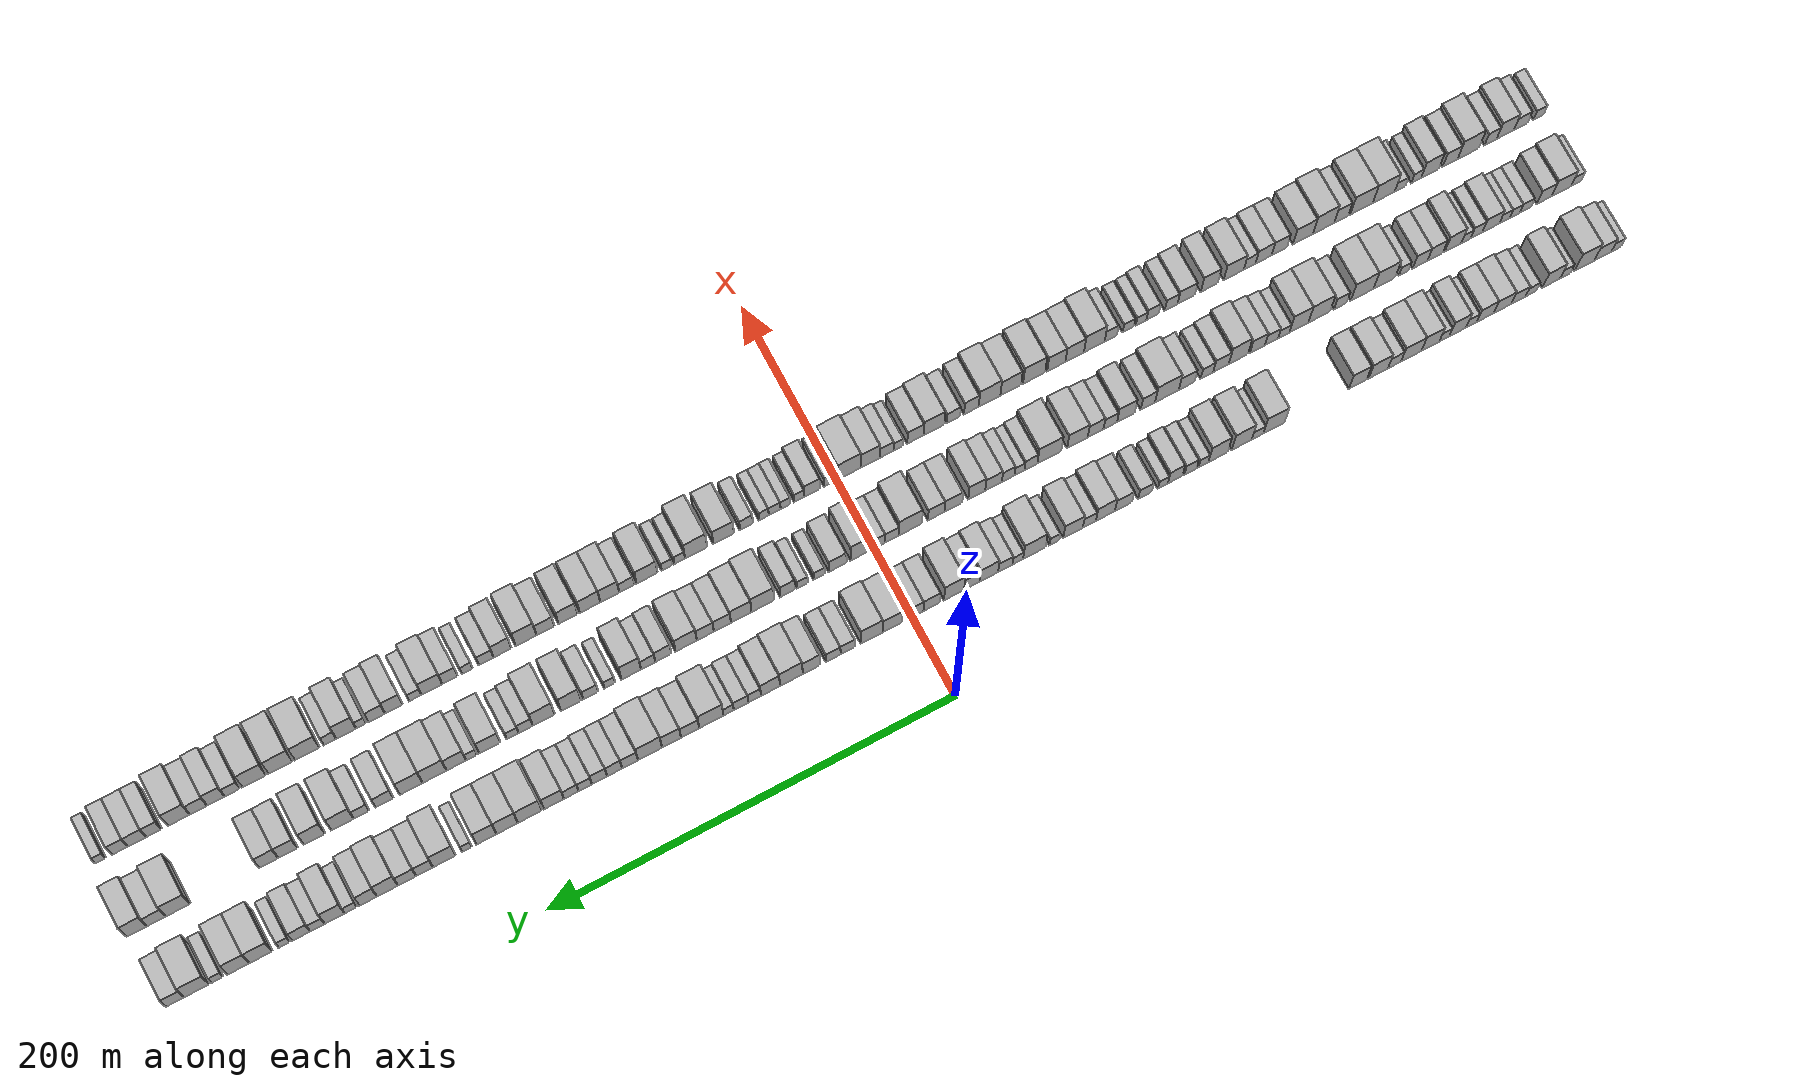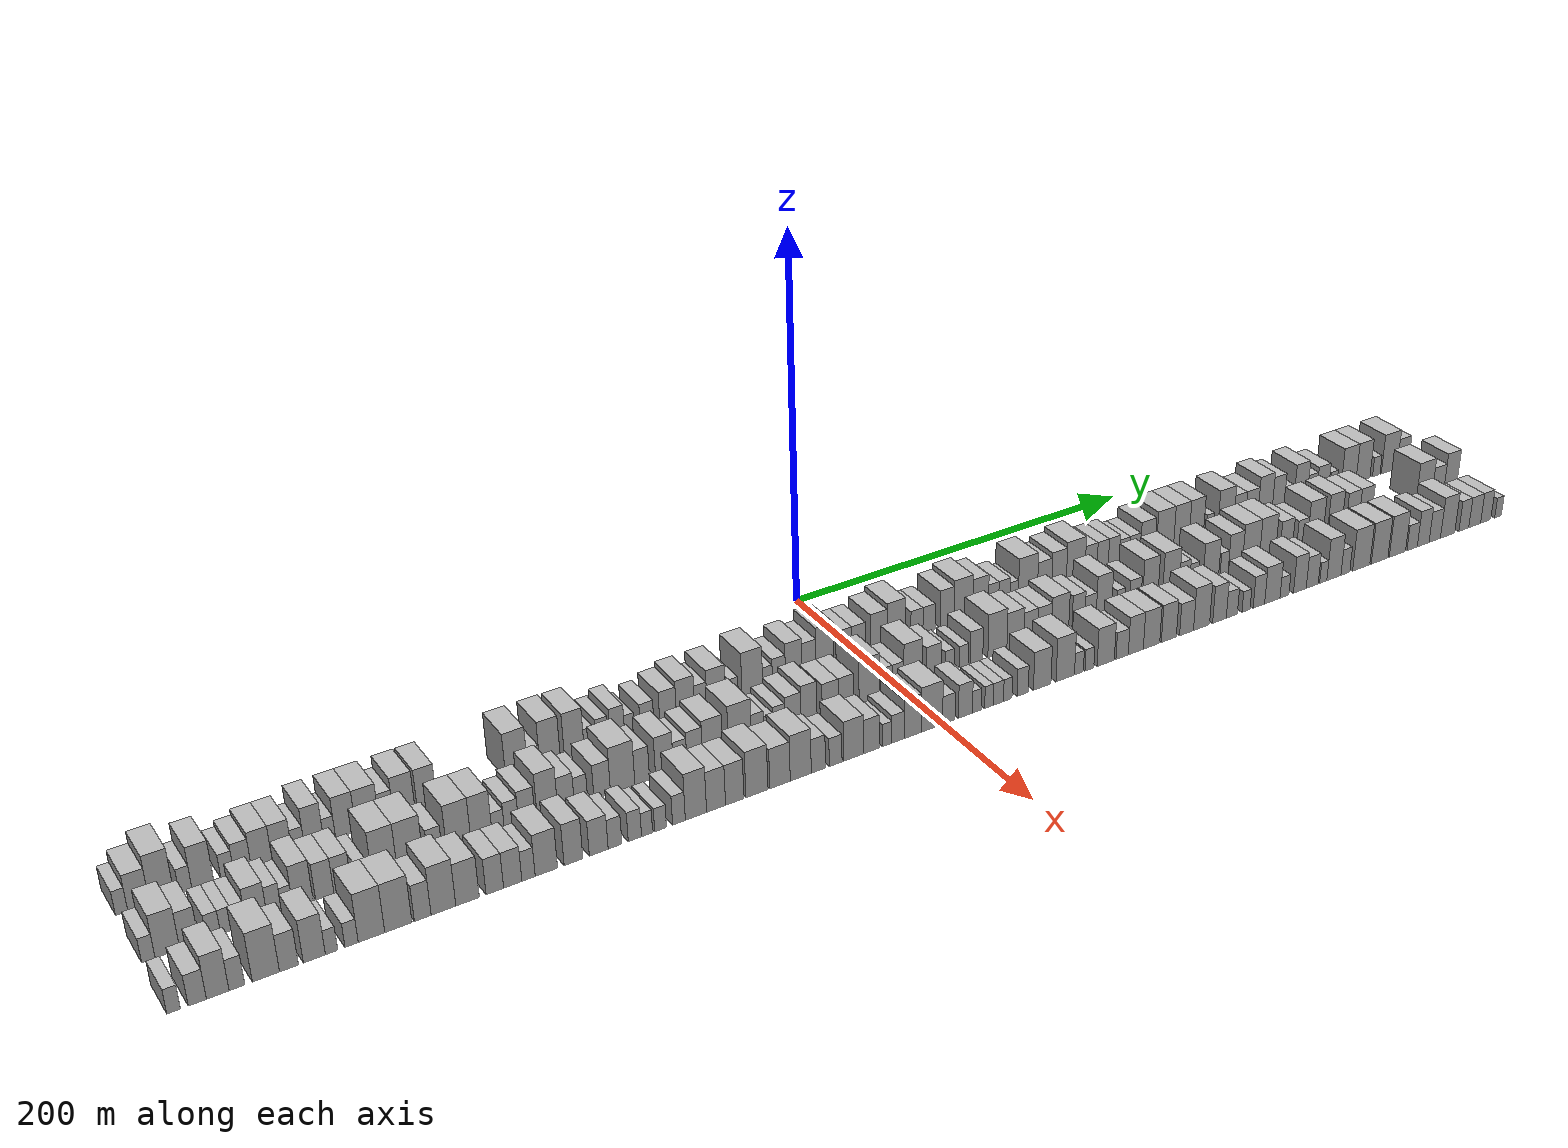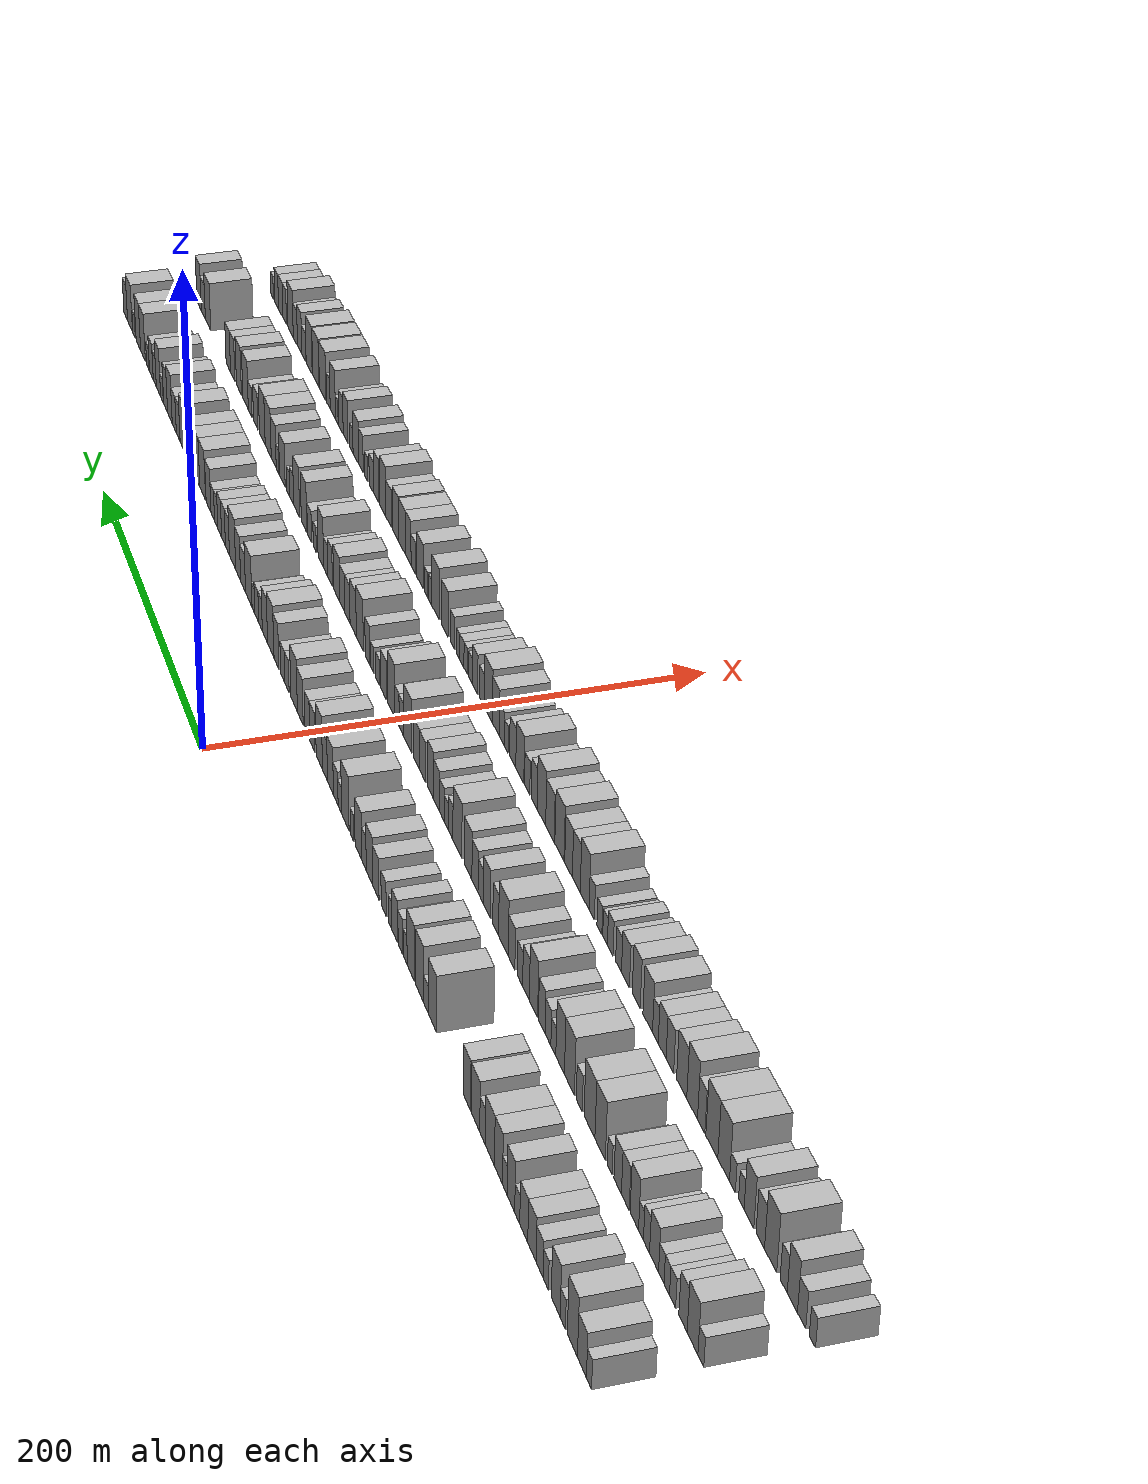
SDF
<sdf version="1.6">
 <world name="default">
  <scene>
   <sky><clouds><speed>12</speed></clouds></sky>
   <ambient>0.4 0.4 0.4 1</ambient>
   <background>0.7 0.7 0.7 1</background>
   <shadows>1</shadows>
  </scene>
  <gravity>0 0 -9.8066</gravity>
  <magnetic_field>6e-06 2.3e-05 -4.2e-05</magnetic_field>
  <physics default="0" name="default_physics" type="ode">
   <ode>
    <solver>
     <type>quick</type>
     <iters>10</iters>
     <sor>1.0</sor>
     <use_dynamic_moi_rescaling>0</use_dynamic_moi_rescaling>
    </solver>
    <constraints>
     <cfm>0</cfm>
     <erp>0.2</erp>
     <contact_max_correcting_vel>100</contact_max_correcting_vel>
     <contact_surface_layer>0.001</contact_surface_layer>
    </constraints>
   </ode>
   <max_step_size>0.004</max_step_size>
   <real_time_factor>1</real_time_factor>
   <real_time_update_rate>250</real_time_update_rate>
  </physics>
  <light name="sun" type="directional">
   <pose>0 0 10 0 0 0</pose>
   <diffuse>0.8 0.8 0.8 1</diffuse>
   <specular>0.2 0.2 0.2 1</specular>
   <attenuation>
    <range>1000</range>
    <constant>0.9</constant>
    <linear>0.01</linear>
    <quadratic>0.001</quadratic>
   </attenuation>
   <direction>-0.5 0.1 -0.9</direction>
  </light>
  <model name="building_1">
   <static>1</static>
   <pose>50.0000 -356.4722 0 0.000000 0.000000 0.000000</pose>
   <link name="link">
    <pose>0 0 6.00 0 0 0</pose>
    <collision name="collision"><geometry><box><size>20.0000 5.0555 12.0000</size></box></geometry></collision>
    <visual name="visual">
     <cast_shadows>0</cast_shadows>
     <geometry><box><size>20.0000 5.0555 12.0000</size></box></geometry>
     <material>
      <script>
       <uri>model://HANNAS_wall/materials/scripts</uri>
       <uri>model://HANNAS_wall/materials/textures</uri>
       <name>vrc/HANNAS_wall</name>
      </script>
     </material>
    </visual>
   </link>
  </model>
  <model name="building_2">
   <static>1</static>
   <pose>50.0000 -349.4609 0 0.000000 0.000000 0.000000</pose>
   <link name="link">
    <pose>0 0 9.00 0 0 0</pose>
    <collision name="collision"><geometry><box><size>20.0000 8.9670 18.0000</size></box></geometry></collision>
    <visual name="visual">
     <cast_shadows>0</cast_shadows>
     <geometry><box><size>20.0000 8.9670 18.0000</size></box></geometry>
     <material>
      <script>
       <uri>model://HANNAS_wall/materials/scripts</uri>
       <uri>model://HANNAS_wall/materials/textures</uri>
       <name>vrc/HANNAS_wall</name>
      </script>
     </material>
    </visual>
   </link>
  </model>
  <model name="building_3">
   <static>1</static>
   <pose>50.0000 -339.8826 0 0.000000 0.000000 0.000000</pose>
   <link name="link">
    <pose>0 0 12.00 0 0 0</pose>
    <collision name="collision"><geometry><box><size>20.0000 10.1896 24.0000</size></box></geometry></collision>
    <visual name="visual">
     <cast_shadows>0</cast_shadows>
     <geometry><box><size>20.0000 10.1896 24.0000</size></box></geometry>
     <material>
      <script>
       <uri>model://HANNAS_wall/materials/scripts</uri>
       <uri>model://HANNAS_wall/materials/textures</uri>
       <name>vrc/HANNAS_wall</name>
      </script>
     </material>
    </visual>
   </link>
  </model>
  <model name="building_4">
   <static>1</static>
   <pose>50.0000 -330.0991 0 0.000000 0.000000 0.000000</pose>
   <link name="link">
    <pose>0 0 6.00 0 0 0</pose>
    <collision name="collision"><geometry><box><size>20.0000 5.3775 12.0000</size></box></geometry></collision>
    <visual name="visual">
     <cast_shadows>0</cast_shadows>
     <geometry><box><size>20.0000 5.3775 12.0000</size></box></geometry>
     <material>
      <script>
       <uri>model://HANNAS_wall/materials/scripts</uri>
       <uri>model://HANNAS_wall/materials/textures</uri>
       <name>vrc/HANNAS_wall</name>
      </script>
     </material>
    </visual>
   </link>
  </model>
  <model name="building_5">
   <static>1</static>
   <pose>50.0000 -322.8088 0 0.000000 0.000000 0.000000</pose>
   <link name="link">
    <pose>0 0 10.50 0 0 0</pose>
    <collision name="collision"><geometry><box><size>20.0000 9.2032 21.0000</size></box></geometry></collision>
    <visual name="visual">
     <cast_shadows>0</cast_shadows>
     <geometry><box><size>20.0000 9.2032 21.0000</size></box></geometry>
     <material>
      <script>
       <uri>model://HANNAS_wall/materials/scripts</uri>
       <uri>model://HANNAS_wall/materials/textures</uri>
       <name>vrc/HANNAS_wall</name>
      </script>
     </material>
    </visual>
   </link>
  </model>
  <model name="building_6">
   <static>1</static>
   <pose>50.0000 -312.4091 0 0.000000 0.000000 0.000000</pose>
   <link name="link">
    <pose>0 0 6.00 0 0 0</pose>
    <collision name="collision"><geometry><box><size>20.0000 5.5962 12.0000</size></box></geometry></collision>
    <visual name="visual">
     <cast_shadows>0</cast_shadows>
     <geometry><box><size>20.0000 5.5962 12.0000</size></box></geometry>
     <material>
      <script>
       <uri>model://HANNAS_wall/materials/scripts</uri>
       <uri>model://HANNAS_wall/materials/textures</uri>
       <name>vrc/HANNAS_wall</name>
      </script>
     </material>
    </visual>
   </link>
  </model>
  <model name="building_7">
   <static>1</static>
   <pose>50.0000 -305.8797 0 0.000000 0.000000 0.000000</pose>
   <link name="link">
    <pose>0 0 7.50 0 0 0</pose>
    <collision name="collision"><geometry><box><size>20.0000 7.4626 15.0000</size></box></geometry></collision>
    <visual name="visual">
     <cast_shadows>0</cast_shadows>
     <geometry><box><size>20.0000 7.4626 15.0000</size></box></geometry>
     <material>
      <script>
       <uri>model://HANNAS_wall/materials/scripts</uri>
       <uri>model://HANNAS_wall/materials/textures</uri>
       <name>vrc/HANNAS_wall</name>
      </script>
     </material>
    </visual>
   </link>
  </model>
  <model name="building_8">
   <static>1</static>
   <pose>50.0000 -297.6605 0 0.000000 0.000000 0.000000</pose>
   <link name="link">
    <pose>0 0 9.00 0 0 0</pose>
    <collision name="collision"><geometry><box><size>20.0000 8.9758 18.0000</size></box></geometry></collision>
    <visual name="visual">
     <cast_shadows>0</cast_shadows>
     <geometry><box><size>20.0000 8.9758 18.0000</size></box></geometry>
     <material>
      <script>
       <uri>model://HANNAS_wall/materials/scripts</uri>
       <uri>model://HANNAS_wall/materials/textures</uri>
       <name>vrc/HANNAS_wall</name>
      </script>
     </material>
    </visual>
   </link>
  </model>
  <model name="building_9">
   <static>1</static>
   <pose>50.0000 -288.8021 0 0.000000 0.000000 0.000000</pose>
   <link name="link">
    <pose>0 0 9.00 0 0 0</pose>
    <collision name="collision"><geometry><box><size>20.0000 8.7409 18.0000</size></box></geometry></collision>
    <visual name="visual">
     <cast_shadows>0</cast_shadows>
     <geometry><box><size>20.0000 8.7409 18.0000</size></box></geometry>
     <material>
      <script>
       <uri>model://HANNAS_wall/materials/scripts</uri>
       <uri>model://HANNAS_wall/materials/textures</uri>
       <name>vrc/HANNAS_wall</name>
      </script>
     </material>
    </visual>
   </link>
  </model>
  <model name="building_10">
   <static>1</static>
   <pose>50.0000 -281.6566 0 0.000000 0.000000 0.000000</pose>
   <link name="link">
    <pose>0 0 6.00 0 0 0</pose>
    <collision name="collision"><geometry><box><size>20.0000 5.5501 12.0000</size></box></geometry></collision>
    <visual name="visual">
     <cast_shadows>0</cast_shadows>
     <geometry><box><size>20.0000 5.5501 12.0000</size></box></geometry>
     <material>
      <script>
       <uri>model://HANNAS_wall/materials/scripts</uri>
       <uri>model://HANNAS_wall/materials/textures</uri>
       <name>vrc/HANNAS_wall</name>
      </script>
     </material>
    </visual>
   </link>
  </model>
  <model name="building_11">
   <static>1</static>
   <pose>50.0000 -274.6455 0 0.000000 0.000000 0.000000</pose>
   <link name="link">
    <pose>0 0 10.50 0 0 0</pose>
    <collision name="collision"><geometry><box><size>20.0000 8.4722 21.0000</size></box></geometry></collision>
    <visual name="visual">
     <cast_shadows>0</cast_shadows>
     <geometry><box><size>20.0000 8.4722 21.0000</size></box></geometry>
     <material>
      <script>
       <uri>model://HANNAS_wall/materials/scripts</uri>
       <uri>model://HANNAS_wall/materials/textures</uri>
       <name>vrc/HANNAS_wall</name>
      </script>
     </material>
    </visual>
   </link>
  </model>
  <model name="building_12">
   <static>1</static>
   <pose>50.0000 -267.8243 0 0.000000 0.000000 0.000000</pose>
   <link name="link">
    <pose>0 0 6.00 0 0 0</pose>
    <collision name="collision"><geometry><box><size>20.0000 5.1701 12.0000</size></box></geometry></collision>
    <visual name="visual">
     <cast_shadows>0</cast_shadows>
     <geometry><box><size>20.0000 5.1701 12.0000</size></box></geometry>
     <material>
      <script>
       <uri>model://HANNAS_wall/materials/scripts</uri>
       <uri>model://HANNAS_wall/materials/textures</uri>
       <name>vrc/HANNAS_wall</name>
      </script>
     </material>
    </visual>
   </link>
  </model>
  <model name="building_13">
   <static>1</static>
   <pose>50.0000 -260.6515 0 0.000000 0.000000 0.000000</pose>
   <link name="link">
    <pose>0 0 10.50 0 0 0</pose>
    <collision name="collision"><geometry><box><size>20.0000 9.1756 21.0000</size></box></geometry></collision>
    <visual name="visual">
     <cast_shadows>0</cast_shadows>
     <geometry><box><size>20.0000 9.1756 21.0000</size></box></geometry>
     <material>
      <script>
       <uri>model://HANNAS_wall/materials/scripts</uri>
       <uri>model://HANNAS_wall/materials/textures</uri>
       <name>vrc/HANNAS_wall</name>
      </script>
     </material>
    </visual>
   </link>
  </model>
  <model name="building_14">
   <static>1</static>
   <pose>50.0000 -250.8220 0 0.000000 0.000000 0.000000</pose>
   <link name="link">
    <pose>0 0 10.50 0 0 0</pose>
    <collision name="collision"><geometry><box><size>20.0000 10.4834 21.0000</size></box></geometry></collision>
    <visual name="visual">
     <cast_shadows>0</cast_shadows>
     <geometry><box><size>20.0000 10.4834 21.0000</size></box></geometry>
     <material>
      <script>
       <uri>model://HANNAS_wall/materials/scripts</uri>
       <uri>model://HANNAS_wall/materials/textures</uri>
       <name>vrc/HANNAS_wall</name>
      </script>
     </material>
    </visual>
   </link>
  </model>
  <model name="building_15">
   <static>1</static>
   <pose>50.0000 -242.2735 0 0.000000 0.000000 0.000000</pose>
   <link name="link">
    <pose>0 0 7.50 0 0 0</pose>
    <collision name="collision"><geometry><box><size>20.0000 6.6137 15.0000</size></box></geometry></collision>
    <visual name="visual">
     <cast_shadows>0</cast_shadows>
     <geometry><box><size>20.0000 6.6137 15.0000</size></box></geometry>
     <material>
      <script>
       <uri>model://HANNAS_wall/materials/scripts</uri>
       <uri>model://HANNAS_wall/materials/textures</uri>
       <name>vrc/HANNAS_wall</name>
      </script>
     </material>
    </visual>
   </link>
  </model>
  <model name="building_16">
   <static>1</static>
   <pose>50.0000 -234.0379 0 0.000000 0.000000 0.000000</pose>
   <link name="link">
    <pose>0 0 10.50 0 0 0</pose>
    <collision name="collision"><geometry><box><size>20.0000 9.8577 21.0000</size></box></geometry></collision>
    <visual name="visual">
     <cast_shadows>0</cast_shadows>
     <geometry><box><size>20.0000 9.8577 21.0000</size></box></geometry>
     <material>
      <script>
       <uri>model://HANNAS_wall/materials/scripts</uri>
       <uri>model://HANNAS_wall/materials/textures</uri>
       <name>vrc/HANNAS_wall</name>
      </script>
     </material>
    </visual>
   </link>
  </model>
  <model name="building_17">
   <static>1</static>
   <pose>50.0000 -223.5714 0 0.000000 0.000000 0.000000</pose>
   <link name="link">
    <pose>0 0 10.50 0 0 0</pose>
    <collision name="collision"><geometry><box><size>20.0000 9.0753 21.0000</size></box></geometry></collision>
    <visual name="visual">
     <cast_shadows>0</cast_shadows>
     <geometry><box><size>20.0000 9.0753 21.0000</size></box></geometry>
     <material>
      <script>
       <uri>model://HANNAS_wall/materials/scripts</uri>
       <uri>model://HANNAS_wall/materials/textures</uri>
       <name>vrc/HANNAS_wall</name>
      </script>
     </material>
    </visual>
   </link>
  </model>
  <model name="building_18">
   <static>1</static>
   <pose>50.0000 -181.0141 0 0.000000 0.000000 0.000000</pose>
   <link name="link">
    <pose>0 0 12.00 0 0 0</pose>
    <collision name="collision"><geometry><box><size>20.0000 10.6797 24.0000</size></box></geometry></collision>
    <visual name="visual">
     <cast_shadows>0</cast_shadows>
     <geometry><box><size>20.0000 10.6797 24.0000</size></box></geometry>
     <material>
      <script>
       <uri>model://HANNAS_wall/materials/scripts</uri>
       <uri>model://HANNAS_wall/materials/textures</uri>
       <name>vrc/HANNAS_wall</name>
      </script>
     </material>
    </visual>
   </link>
  </model>
  <model name="building_19">
   <static>1</static>
   <pose>50.0000 -172.7098 0 0.000000 0.000000 0.000000</pose>
   <link name="link">
    <pose>0 0 6.00 0 0 0</pose>
    <collision name="collision"><geometry><box><size>20.0000 5.9289 12.0000</size></box></geometry></collision>
    <visual name="visual">
     <cast_shadows>0</cast_shadows>
     <geometry><box><size>20.0000 5.9289 12.0000</size></box></geometry>
     <material>
      <script>
       <uri>model://HANNAS_wall/materials/scripts</uri>
       <uri>model://HANNAS_wall/materials/textures</uri>
       <name>vrc/HANNAS_wall</name>
      </script>
     </material>
    </visual>
   </link>
  </model>
  <model name="building_20">
   <static>1</static>
   <pose>50.0000 -164.6984 0 0.000000 0.000000 0.000000</pose>
   <link name="link">
    <pose>0 0 12.00 0 0 0</pose>
    <collision name="collision"><geometry><box><size>20.0000 10.0939 24.0000</size></box></geometry></collision>
    <visual name="visual">
     <cast_shadows>0</cast_shadows>
     <geometry><box><size>20.0000 10.0939 24.0000</size></box></geometry>
     <material>
      <script>
       <uri>model://HANNAS_wall/materials/scripts</uri>
       <uri>model://HANNAS_wall/materials/textures</uri>
       <name>vrc/HANNAS_wall</name>
      </script>
     </material>
    </visual>
   </link>
  </model>
  <model name="building_21">
   <static>1</static>
   <pose>50.0000 -152.7551 0 0.000000 0.000000 0.000000</pose>
   <link name="link">
    <pose>0 0 12.00 0 0 0</pose>
    <collision name="collision"><geometry><box><size>20.0000 9.7928 24.0000</size></box></geometry></collision>
    <visual name="visual">
     <cast_shadows>0</cast_shadows>
     <geometry><box><size>20.0000 9.7928 24.0000</size></box></geometry>
     <material>
      <script>
       <uri>model://HANNAS_wall/materials/scripts</uri>
       <uri>model://HANNAS_wall/materials/textures</uri>
       <name>vrc/HANNAS_wall</name>
      </script>
     </material>
    </visual>
   </link>
  </model>
  <model name="building_22">
   <static>1</static>
   <pose>50.0000 -145.3392 0 0.000000 0.000000 0.000000</pose>
   <link name="link">
    <pose>0 0 6.00 0 0 0</pose>
    <collision name="collision"><geometry><box><size>20.0000 5.0390 12.0000</size></box></geometry></collision>
    <visual name="visual">
     <cast_shadows>0</cast_shadows>
     <geometry><box><size>20.0000 5.0390 12.0000</size></box></geometry>
     <material>
      <script>
       <uri>model://HANNAS_wall/materials/scripts</uri>
       <uri>model://HANNAS_wall/materials/textures</uri>
       <name>vrc/HANNAS_wall</name>
      </script>
     </material>
    </visual>
   </link>
  </model>
  <model name="building_23">
   <static>1</static>
   <pose>50.0000 -138.7848 0 0.000000 0.000000 0.000000</pose>
   <link name="link">
    <pose>0 0 7.50 0 0 0</pose>
    <collision name="collision"><geometry><box><size>20.0000 6.0698 15.0000</size></box></geometry></collision>
    <visual name="visual">
     <cast_shadows>0</cast_shadows>
     <geometry><box><size>20.0000 6.0698 15.0000</size></box></geometry>
     <material>
      <script>
       <uri>model://HANNAS_wall/materials/scripts</uri>
       <uri>model://HANNAS_wall/materials/textures</uri>
       <name>vrc/HANNAS_wall</name>
      </script>
     </material>
    </visual>
   </link>
  </model>
  <model name="building_24">
   <static>1</static>
   <pose>50.0000 -131.0683 0 0.000000 0.000000 0.000000</pose>
   <link name="link">
    <pose>0 0 9.00 0 0 0</pose>
    <collision name="collision"><geometry><box><size>20.0000 7.3630 18.0000</size></box></geometry></collision>
    <visual name="visual">
     <cast_shadows>0</cast_shadows>
     <geometry><box><size>20.0000 7.3630 18.0000</size></box></geometry>
     <material>
      <script>
       <uri>model://HANNAS_wall/materials/scripts</uri>
       <uri>model://HANNAS_wall/materials/textures</uri>
       <name>vrc/HANNAS_wall</name>
      </script>
     </material>
    </visual>
   </link>
  </model>
  <model name="building_25">
   <static>1</static>
   <pose>50.0000 -124.8962 0 0.000000 0.000000 0.000000</pose>
   <link name="link">
    <pose>0 0 6.00 0 0 0</pose>
    <collision name="collision"><geometry><box><size>20.0000 4.9811 12.0000</size></box></geometry></collision>
    <visual name="visual">
     <cast_shadows>0</cast_shadows>
     <geometry><box><size>20.0000 4.9811 12.0000</size></box></geometry>
     <material>
      <script>
       <uri>model://HANNAS_wall/materials/scripts</uri>
       <uri>model://HANNAS_wall/materials/textures</uri>
       <name>vrc/HANNAS_wall</name>
      </script>
     </material>
    </visual>
   </link>
  </model>
  <model name="building_26">
   <static>1</static>
   <pose>50.0000 -115.9093 0 0.000000 0.000000 0.000000</pose>
   <link name="link">
    <pose>0 0 7.50 0 0 0</pose>
    <collision name="collision"><geometry><box><size>20.0000 6.9926 15.0000</size></box></geometry></collision>
    <visual name="visual">
     <cast_shadows>0</cast_shadows>
     <geometry><box><size>20.0000 6.9926 15.0000</size></box></geometry>
     <material>
      <script>
       <uri>model://HANNAS_wall/materials/scripts</uri>
       <uri>model://HANNAS_wall/materials/textures</uri>
       <name>vrc/HANNAS_wall</name>
      </script>
     </material>
    </visual>
   </link>
  </model>
  <model name="building_27">
   <static>1</static>
   <pose>50.0000 -105.0629 0 0.000000 0.000000 0.000000</pose>
   <link name="link">
    <pose>0 0 9.00 0 0 0</pose>
    <collision name="collision"><geometry><box><size>20.0000 8.7003 18.0000</size></box></geometry></collision>
    <visual name="visual">
     <cast_shadows>0</cast_shadows>
     <geometry><box><size>20.0000 8.7003 18.0000</size></box></geometry>
     <material>
      <script>
       <uri>model://HANNAS_wall/materials/scripts</uri>
       <uri>model://HANNAS_wall/materials/textures</uri>
       <name>vrc/HANNAS_wall</name>
      </script>
     </material>
    </visual>
   </link>
  </model>
  <model name="building_28">
   <static>1</static>
   <pose>50.0000 -95.9470 0 0.000000 0.000000 0.000000</pose>
   <link name="link">
    <pose>0 0 10.50 0 0 0</pose>
    <collision name="collision"><geometry><box><size>20.0000 9.5315 21.0000</size></box></geometry></collision>
    <visual name="visual">
     <cast_shadows>0</cast_shadows>
     <geometry><box><size>20.0000 9.5315 21.0000</size></box></geometry>
     <material>
      <script>
       <uri>model://HANNAS_wall/materials/scripts</uri>
       <uri>model://HANNAS_wall/materials/textures</uri>
       <name>vrc/HANNAS_wall</name>
      </script>
     </material>
    </visual>
   </link>
  </model>
  <model name="building_29">
   <static>1</static>
   <pose>50.0000 -87.9346 0 0.000000 0.000000 0.000000</pose>
   <link name="link">
    <pose>0 0 7.50 0 0 0</pose>
    <collision name="collision"><geometry><box><size>20.0000 6.4934 15.0000</size></box></geometry></collision>
    <visual name="visual">
     <cast_shadows>0</cast_shadows>
     <geometry><box><size>20.0000 6.4934 15.0000</size></box></geometry>
     <material>
      <script>
       <uri>model://HANNAS_wall/materials/scripts</uri>
       <uri>model://HANNAS_wall/materials/textures</uri>
       <name>vrc/HANNAS_wall</name>
      </script>
     </material>
    </visual>
   </link>
  </model>
  <model name="building_30">
   <static>1</static>
   <pose>50.0000 -79.7964 0 0.000000 0.000000 0.000000</pose>
   <link name="link">
    <pose>0 0 10.50 0 0 0</pose>
    <collision name="collision"><geometry><box><size>20.0000 9.7829 21.0000</size></box></geometry></collision>
    <visual name="visual">
     <cast_shadows>0</cast_shadows>
     <geometry><box><size>20.0000 9.7829 21.0000</size></box></geometry>
     <material>
      <script>
       <uri>model://HANNAS_wall/materials/scripts</uri>
       <uri>model://HANNAS_wall/materials/textures</uri>
       <name>vrc/HANNAS_wall</name>
      </script>
     </material>
    </visual>
   </link>
  </model>
  <model name="building_31">
   <static>1</static>
   <pose>50.0000 -70.4690 0 0.000000 0.000000 0.000000</pose>
   <link name="link">
    <pose>0 0 6.00 0 0 0</pose>
    <collision name="collision"><geometry><box><size>20.0000 4.8719 12.0000</size></box></geometry></collision>
    <visual name="visual">
     <cast_shadows>0</cast_shadows>
     <geometry><box><size>20.0000 4.8719 12.0000</size></box></geometry>
     <material>
      <script>
       <uri>model://HANNAS_wall/materials/scripts</uri>
       <uri>model://HANNAS_wall/materials/textures</uri>
       <name>vrc/HANNAS_wall</name>
      </script>
     </material>
    </visual>
   </link>
  </model>
  <model name="building_32">
   <static>1</static>
   <pose>50.0000 -60.4314 0 0.000000 0.000000 0.000000</pose>
   <link name="link">
    <pose>0 0 12.00 0 0 0</pose>
    <collision name="collision"><geometry><box><size>20.0000 11.2034 24.0000</size></box></geometry></collision>
    <visual name="visual">
     <cast_shadows>0</cast_shadows>
     <geometry><box><size>20.0000 11.2034 24.0000</size></box></geometry>
     <material>
      <script>
       <uri>model://HANNAS_wall/materials/scripts</uri>
       <uri>model://HANNAS_wall/materials/textures</uri>
       <name>vrc/HANNAS_wall</name>
      </script>
     </material>
    </visual>
   </link>
  </model>
  <model name="building_33">
   <static>1</static>
   <pose>50.0000 -52.1777 0 0.000000 0.000000 0.000000</pose>
   <link name="link">
    <pose>0 0 6.00 0 0 0</pose>
    <collision name="collision"><geometry><box><size>20.0000 5.3040 12.0000</size></box></geometry></collision>
    <visual name="visual">
     <cast_shadows>0</cast_shadows>
     <geometry><box><size>20.0000 5.3040 12.0000</size></box></geometry>
     <material>
      <script>
       <uri>model://HANNAS_wall/materials/scripts</uri>
       <uri>model://HANNAS_wall/materials/textures</uri>
       <name>vrc/HANNAS_wall</name>
      </script>
     </material>
    </visual>
   </link>
  </model>
  <model name="building_34">
   <static>1</static>
   <pose>50.0000 -45.9493 0 0.000000 0.000000 0.000000</pose>
   <link name="link">
    <pose>0 0 7.50 0 0 0</pose>
    <collision name="collision"><geometry><box><size>20.0000 7.1527 15.0000</size></box></geometry></collision>
    <visual name="visual">
     <cast_shadows>0</cast_shadows>
     <geometry><box><size>20.0000 7.1527 15.0000</size></box></geometry>
     <material>
      <script>
       <uri>model://HANNAS_wall/materials/scripts</uri>
       <uri>model://HANNAS_wall/materials/textures</uri>
       <name>vrc/HANNAS_wall</name>
      </script>
     </material>
    </visual>
   </link>
  </model>
  <model name="building_35">
   <static>1</static>
   <pose>50.0000 -37.8079 0 0.000000 0.000000 0.000000</pose>
   <link name="link">
    <pose>0 0 10.50 0 0 0</pose>
    <collision name="collision"><geometry><box><size>20.0000 9.1302 21.0000</size></box></geometry></collision>
    <visual name="visual">
     <cast_shadows>0</cast_shadows>
     <geometry><box><size>20.0000 9.1302 21.0000</size></box></geometry>
     <material>
      <script>
       <uri>model://HANNAS_wall/materials/scripts</uri>
       <uri>model://HANNAS_wall/materials/textures</uri>
       <name>vrc/HANNAS_wall</name>
      </script>
     </material>
    </visual>
   </link>
  </model>
  <model name="building_36">
   <static>1</static>
   <pose>50.0000 -29.3326 0 0.000000 0.000000 0.000000</pose>
   <link name="link">
    <pose>0 0 9.00 0 0 0</pose>
    <collision name="collision"><geometry><box><size>20.0000 7.8204 18.0000</size></box></geometry></collision>
    <visual name="visual">
     <cast_shadows>0</cast_shadows>
     <geometry><box><size>20.0000 7.8204 18.0000</size></box></geometry>
     <material>
      <script>
       <uri>model://HANNAS_wall/materials/scripts</uri>
       <uri>model://HANNAS_wall/materials/textures</uri>
       <name>vrc/HANNAS_wall</name>
      </script>
     </material>
    </visual>
   </link>
  </model>
  <model name="building_37">
   <static>1</static>
   <pose>50.0000 -20.4561 0 0.000000 0.000000 0.000000</pose>
   <link name="link">
    <pose>0 0 12.00 0 0 0</pose>
    <collision name="collision"><geometry><box><size>20.0000 9.9324 24.0000</size></box></geometry></collision>
    <visual name="visual">
     <cast_shadows>0</cast_shadows>
     <geometry><box><size>20.0000 9.9324 24.0000</size></box></geometry>
     <material>
      <script>
       <uri>model://HANNAS_wall/materials/scripts</uri>
       <uri>model://HANNAS_wall/materials/textures</uri>
       <name>vrc/HANNAS_wall</name>
      </script>
     </material>
    </visual>
   </link>
  </model>
  <model name="building_38">
   <static>1</static>
   <pose>50.0000 -9.3580 0 0.000000 0.000000 0.000000</pose>
   <link name="link">
    <pose>0 0 9.00 0 0 0</pose>
    <collision name="collision"><geometry><box><size>20.0000 8.2639 18.0000</size></box></geometry></collision>
    <visual name="visual">
     <cast_shadows>0</cast_shadows>
     <geometry><box><size>20.0000 8.2639 18.0000</size></box></geometry>
     <material>
      <script>
       <uri>model://HANNAS_wall/materials/scripts</uri>
       <uri>model://HANNAS_wall/materials/textures</uri>
       <name>vrc/HANNAS_wall</name>
      </script>
     </material>
    </visual>
   </link>
  </model>
  <model name="building_39">
   <static>1</static>
   <pose>50.0000 -1.3939 0 0.000000 0.000000 0.000000</pose>
   <link name="link">
    <pose>0 0 9.00 0 0 0</pose>
    <collision name="collision"><geometry><box><size>20.0000 7.6644 18.0000</size></box></geometry></collision>
    <visual name="visual">
     <cast_shadows>0</cast_shadows>
     <geometry><box><size>20.0000 7.6644 18.0000</size></box></geometry>
     <material>
      <script>
       <uri>model://HANNAS_wall/materials/scripts</uri>
       <uri>model://HANNAS_wall/materials/textures</uri>
       <name>vrc/HANNAS_wall</name>
      </script>
     </material>
    </visual>
   </link>
  </model>
  <model name="building_40">
   <static>1</static>
   <pose>50.0000 10.1830 0 0.000000 0.000000 0.000000</pose>
   <link name="link">
    <pose>0 0 10.50 0 0 0</pose>
    <collision name="collision"><geometry><box><size>20.0000 9.4892 21.0000</size></box></geometry></collision>
    <visual name="visual">
     <cast_shadows>0</cast_shadows>
     <geometry><box><size>20.0000 9.4892 21.0000</size></box></geometry>
     <material>
      <script>
       <uri>model://HANNAS_wall/materials/scripts</uri>
       <uri>model://HANNAS_wall/materials/textures</uri>
       <name>vrc/HANNAS_wall</name>
      </script>
     </material>
    </visual>
   </link>
  </model>
  <model name="building_41">
   <static>1</static>
   <pose>50.0000 20.3024 0 0.000000 0.000000 0.000000</pose>
   <link name="link">
    <pose>0 0 12.00 0 0 0</pose>
    <collision name="collision"><geometry><box><size>20.0000 10.7497 24.0000</size></box></geometry></collision>
    <visual name="visual">
     <cast_shadows>0</cast_shadows>
     <geometry><box><size>20.0000 10.7497 24.0000</size></box></geometry>
     <material>
      <script>
       <uri>model://HANNAS_wall/materials/scripts</uri>
       <uri>model://HANNAS_wall/materials/textures</uri>
       <name>vrc/HANNAS_wall</name>
      </script>
     </material>
    </visual>
   </link>
  </model>
  <model name="building_42">
   <static>1</static>
   <pose>50.0000 32.2145 0 0.000000 0.000000 0.000000</pose>
   <link name="link">
    <pose>0 0 7.50 0 0 0</pose>
    <collision name="collision"><geometry><box><size>20.0000 7.0744 15.0000</size></box></geometry></collision>
    <visual name="visual">
     <cast_shadows>0</cast_shadows>
     <geometry><box><size>20.0000 7.0744 15.0000</size></box></geometry>
     <material>
      <script>
       <uri>model://HANNAS_wall/materials/scripts</uri>
       <uri>model://HANNAS_wall/materials/textures</uri>
       <name>vrc/HANNAS_wall</name>
      </script>
     </material>
    </visual>
   </link>
  </model>
  <model name="building_43">
   <static>1</static>
   <pose>50.0000 39.3322 0 0.000000 0.000000 0.000000</pose>
   <link name="link">
    <pose>0 0 7.50 0 0 0</pose>
    <collision name="collision"><geometry><box><size>20.0000 7.1611 15.0000</size></box></geometry></collision>
    <visual name="visual">
     <cast_shadows>0</cast_shadows>
     <geometry><box><size>20.0000 7.1611 15.0000</size></box></geometry>
     <material>
      <script>
       <uri>model://HANNAS_wall/materials/scripts</uri>
       <uri>model://HANNAS_wall/materials/textures</uri>
       <name>vrc/HANNAS_wall</name>
      </script>
     </material>
    </visual>
   </link>
  </model>
  <model name="building_44">
   <static>1</static>
   <pose>50.0000 50.1427 0 0.000000 0.000000 0.000000</pose>
   <link name="link">
    <pose>0 0 10.50 0 0 0</pose>
    <collision name="collision"><geometry><box><size>20.0000 8.4600 21.0000</size></box></geometry></collision>
    <visual name="visual">
     <cast_shadows>0</cast_shadows>
     <geometry><box><size>20.0000 8.4600 21.0000</size></box></geometry>
     <material>
      <script>
       <uri>model://HANNAS_wall/materials/scripts</uri>
       <uri>model://HANNAS_wall/materials/textures</uri>
       <name>vrc/HANNAS_wall</name>
      </script>
     </material>
    </visual>
   </link>
  </model>
  <model name="building_45">
   <static>1</static>
   <pose>50.0000 59.9596 0 0.000000 0.000000 0.000000</pose>
   <link name="link">
    <pose>0 0 12.00 0 0 0</pose>
    <collision name="collision"><geometry><box><size>20.0000 11.1738 24.0000</size></box></geometry></collision>
    <visual name="visual">
     <cast_shadows>0</cast_shadows>
     <geometry><box><size>20.0000 11.1738 24.0000</size></box></geometry>
     <material>
      <script>
       <uri>model://HANNAS_wall/materials/scripts</uri>
       <uri>model://HANNAS_wall/materials/textures</uri>
       <name>vrc/HANNAS_wall</name>
      </script>
     </material>
    </visual>
   </link>
  </model>
  <model name="building_46">
   <static>1</static>
   <pose>50.0000 70.2104 0 0.000000 0.000000 0.000000</pose>
   <link name="link">
    <pose>0 0 10.50 0 0 0</pose>
    <collision name="collision"><geometry><box><size>20.0000 9.3278 21.0000</size></box></geometry></collision>
    <visual name="visual">
     <cast_shadows>0</cast_shadows>
     <geometry><box><size>20.0000 9.3278 21.0000</size></box></geometry>
     <material>
      <script>
       <uri>model://HANNAS_wall/materials/scripts</uri>
       <uri>model://HANNAS_wall/materials/textures</uri>
       <name>vrc/HANNAS_wall</name>
      </script>
     </material>
    </visual>
   </link>
  </model>
  <model name="building_47">
   <static>1</static>
   <pose>50.0000 77.9958 0 0.000000 0.000000 0.000000</pose>
   <link name="link">
    <pose>0 0 7.50 0 0 0</pose>
    <collision name="collision"><geometry><box><size>20.0000 6.2429 15.0000</size></box></geometry></collision>
    <visual name="visual">
     <cast_shadows>0</cast_shadows>
     <geometry><box><size>20.0000 6.2429 15.0000</size></box></geometry>
     <material>
      <script>
       <uri>model://HANNAS_wall/materials/scripts</uri>
       <uri>model://HANNAS_wall/materials/textures</uri>
       <name>vrc/HANNAS_wall</name>
      </script>
     </material>
    </visual>
   </link>
  </model>
  <model name="building_48">
   <static>1</static>
   <pose>50.0000 84.6650 0 0.000000 0.000000 0.000000</pose>
   <link name="link">
    <pose>0 0 7.50 0 0 0</pose>
    <collision name="collision"><geometry><box><size>20.0000 7.0955 15.0000</size></box></geometry></collision>
    <visual name="visual">
     <cast_shadows>0</cast_shadows>
     <geometry><box><size>20.0000 7.0955 15.0000</size></box></geometry>
     <material>
      <script>
       <uri>model://HANNAS_wall/materials/scripts</uri>
       <uri>model://HANNAS_wall/materials/textures</uri>
       <name>vrc/HANNAS_wall</name>
      </script>
     </material>
    </visual>
   </link>
  </model>
  <model name="building_49">
   <static>1</static>
   <pose>50.0000 90.7321 0 0.000000 0.000000 0.000000</pose>
   <link name="link">
    <pose>0 0 6.00 0 0 0</pose>
    <collision name="collision"><geometry><box><size>20.0000 5.0387 12.0000</size></box></geometry></collision>
    <visual name="visual">
     <cast_shadows>0</cast_shadows>
     <geometry><box><size>20.0000 5.0387 12.0000</size></box></geometry>
     <material>
      <script>
       <uri>model://HANNAS_wall/materials/scripts</uri>
       <uri>model://HANNAS_wall/materials/textures</uri>
       <name>vrc/HANNAS_wall</name>
      </script>
     </material>
    </visual>
   </link>
  </model>
  <model name="building_50">
   <static>1</static>
   <pose>50.0000 99.1785 0 0.000000 0.000000 0.000000</pose>
   <link name="link">
    <pose>0 0 12.00 0 0 0</pose>
    <collision name="collision"><geometry><box><size>20.0000 11.8541 24.0000</size></box></geometry></collision>
    <visual name="visual">
     <cast_shadows>0</cast_shadows>
     <geometry><box><size>20.0000 11.8541 24.0000</size></box></geometry>
     <material>
      <script>
       <uri>model://HANNAS_wall/materials/scripts</uri>
       <uri>model://HANNAS_wall/materials/textures</uri>
       <name>vrc/HANNAS_wall</name>
      </script>
     </material>
    </visual>
   </link>
  </model>
  <model name="building_51">
   <static>1</static>
   <pose>50.0000 109.5695 0 0.000000 0.000000 0.000000</pose>
   <link name="link">
    <pose>0 0 9.00 0 0 0</pose>
    <collision name="collision"><geometry><box><size>20.0000 8.9278 18.0000</size></box></geometry></collision>
    <visual name="visual">
     <cast_shadows>0</cast_shadows>
     <geometry><box><size>20.0000 8.9278 18.0000</size></box></geometry>
     <material>
      <script>
       <uri>model://HANNAS_wall/materials/scripts</uri>
       <uri>model://HANNAS_wall/materials/textures</uri>
       <name>vrc/HANNAS_wall</name>
      </script>
     </material>
    </visual>
   </link>
  </model>
  <model name="building_52">
   <static>1</static>
   <pose>50.0000 118.6475 0 0.000000 0.000000 0.000000</pose>
   <link name="link">
    <pose>0 0 10.50 0 0 0</pose>
    <collision name="collision"><geometry><box><size>20.0000 9.2281 21.0000</size></box></geometry></collision>
    <visual name="visual">
     <cast_shadows>0</cast_shadows>
     <geometry><box><size>20.0000 9.2281 21.0000</size></box></geometry>
     <material>
      <script>
       <uri>model://HANNAS_wall/materials/scripts</uri>
       <uri>model://HANNAS_wall/materials/textures</uri>
       <name>vrc/HANNAS_wall</name>
      </script>
     </material>
    </visual>
   </link>
  </model>
  <model name="building_53">
   <static>1</static>
   <pose>50.0000 129.1601 0 0.000000 0.000000 0.000000</pose>
   <link name="link">
    <pose>0 0 12.00 0 0 0</pose>
    <collision name="collision"><geometry><box><size>20.0000 11.7972 24.0000</size></box></geometry></collision>
    <visual name="visual">
     <cast_shadows>0</cast_shadows>
     <geometry><box><size>20.0000 11.7972 24.0000</size></box></geometry>
     <material>
      <script>
       <uri>model://HANNAS_wall/materials/scripts</uri>
       <uri>model://HANNAS_wall/materials/textures</uri>
       <name>vrc/HANNAS_wall</name>
      </script>
     </material>
    </visual>
   </link>
  </model>
  <model name="building_54">
   <static>1</static>
   <pose>50.0000 138.9152 0 0.000000 0.000000 0.000000</pose>
   <link name="link">
    <pose>0 0 9.00 0 0 0</pose>
    <collision name="collision"><geometry><box><size>20.0000 7.7130 18.0000</size></box></geometry></collision>
    <visual name="visual">
     <cast_shadows>0</cast_shadows>
     <geometry><box><size>20.0000 7.7130 18.0000</size></box></geometry>
     <material>
      <script>
       <uri>model://HANNAS_wall/materials/scripts</uri>
       <uri>model://HANNAS_wall/materials/textures</uri>
       <name>vrc/HANNAS_wall</name>
      </script>
     </material>
    </visual>
   </link>
  </model>
  <model name="building_55">
   <static>1</static>
   <pose>50.0000 146.4162 0 0.000000 0.000000 0.000000</pose>
   <link name="link">
    <pose>0 0 9.00 0 0 0</pose>
    <collision name="collision"><geometry><box><size>20.0000 7.2892 18.0000</size></box></geometry></collision>
    <visual name="visual">
     <cast_shadows>0</cast_shadows>
     <geometry><box><size>20.0000 7.2892 18.0000</size></box></geometry>
     <material>
      <script>
       <uri>model://HANNAS_wall/materials/scripts</uri>
       <uri>model://HANNAS_wall/materials/textures</uri>
       <name>vrc/HANNAS_wall</name>
      </script>
     </material>
    </visual>
   </link>
  </model>
  <model name="building_56">
   <static>1</static>
   <pose>50.0000 153.7322 0 0.000000 0.000000 0.000000</pose>
   <link name="link">
    <pose>0 0 9.00 0 0 0</pose>
    <collision name="collision"><geometry><box><size>20.0000 7.3428 18.0000</size></box></geometry></collision>
    <visual name="visual">
     <cast_shadows>0</cast_shadows>
     <geometry><box><size>20.0000 7.3428 18.0000</size></box></geometry>
     <material>
      <script>
       <uri>model://HANNAS_wall/materials/scripts</uri>
       <uri>model://HANNAS_wall/materials/textures</uri>
       <name>vrc/HANNAS_wall</name>
      </script>
     </material>
    </visual>
   </link>
  </model>
  <model name="building_57">
   <static>1</static>
   <pose>50.0000 160.6689 0 0.000000 0.000000 0.000000</pose>
   <link name="link">
    <pose>0 0 7.50 0 0 0</pose>
    <collision name="collision"><geometry><box><size>20.0000 6.5305 15.0000</size></box></geometry></collision>
    <visual name="visual">
     <cast_shadows>0</cast_shadows>
     <geometry><box><size>20.0000 6.5305 15.0000</size></box></geometry>
     <material>
      <script>
       <uri>model://HANNAS_wall/materials/scripts</uri>
       <uri>model://HANNAS_wall/materials/textures</uri>
       <name>vrc/HANNAS_wall</name>
      </script>
     </material>
    </visual>
   </link>
  </model>
  <model name="building_58">
   <static>1</static>
   <pose>50.0000 167.4684 0 0.000000 0.000000 0.000000</pose>
   <link name="link">
    <pose>0 0 7.50 0 0 0</pose>
    <collision name="collision"><geometry><box><size>20.0000 7.0686 15.0000</size></box></geometry></collision>
    <visual name="visual">
     <cast_shadows>0</cast_shadows>
     <geometry><box><size>20.0000 7.0686 15.0000</size></box></geometry>
     <material>
      <script>
       <uri>model://HANNAS_wall/materials/scripts</uri>
       <uri>model://HANNAS_wall/materials/textures</uri>
       <name>vrc/HANNAS_wall</name>
      </script>
     </material>
    </visual>
   </link>
  </model>
  <model name="building_59">
   <static>1</static>
   <pose>50.0000 175.8399 0 0.000000 0.000000 0.000000</pose>
   <link name="link">
    <pose>0 0 10.50 0 0 0</pose>
    <collision name="collision"><geometry><box><size>20.0000 9.6744 21.0000</size></box></geometry></collision>
    <visual name="visual">
     <cast_shadows>0</cast_shadows>
     <geometry><box><size>20.0000 9.6744 21.0000</size></box></geometry>
     <material>
      <script>
       <uri>model://HANNAS_wall/materials/scripts</uri>
       <uri>model://HANNAS_wall/materials/textures</uri>
       <name>vrc/HANNAS_wall</name>
      </script>
     </material>
    </visual>
   </link>
  </model>
  <model name="building_60">
   <static>1</static>
   <pose>50.0000 187.4955 0 0.000000 0.000000 0.000000</pose>
   <link name="link">
    <pose>0 0 12.00 0 0 0</pose>
    <collision name="collision"><geometry><box><size>20.0000 11.6368 24.0000</size></box></geometry></collision>
    <visual name="visual">
     <cast_shadows>0</cast_shadows>
     <geometry><box><size>20.0000 11.6368 24.0000</size></box></geometry>
     <material>
      <script>
       <uri>model://HANNAS_wall/materials/scripts</uri>
       <uri>model://HANNAS_wall/materials/textures</uri>
       <name>vrc/HANNAS_wall</name>
      </script>
     </material>
    </visual>
   </link>
  </model>
  <model name="building_61">
   <static>1</static>
   <pose>50.0000 198.5127 0 0.000000 0.000000 0.000000</pose>
   <link name="link">
    <pose>0 0 12.00 0 0 0</pose>
    <collision name="collision"><geometry><box><size>20.0000 10.3974 24.0000</size></box></geometry></collision>
    <visual name="visual">
     <cast_shadows>0</cast_shadows>
     <geometry><box><size>20.0000 10.3974 24.0000</size></box></geometry>
     <material>
      <script>
       <uri>model://HANNAS_wall/materials/scripts</uri>
       <uri>model://HANNAS_wall/materials/textures</uri>
       <name>vrc/HANNAS_wall</name>
      </script>
     </material>
    </visual>
   </link>
  </model>
  <model name="building_62">
   <static>1</static>
   <pose>50.0000 208.5601 0 0.000000 0.000000 0.000000</pose>
   <link name="link">
    <pose>0 0 12.00 0 0 0</pose>
    <collision name="collision"><geometry><box><size>20.0000 9.6974 24.0000</size></box></geometry></collision>
    <visual name="visual">
     <cast_shadows>0</cast_shadows>
     <geometry><box><size>20.0000 9.6974 24.0000</size></box></geometry>
     <material>
      <script>
       <uri>model://HANNAS_wall/materials/scripts</uri>
       <uri>model://HANNAS_wall/materials/textures</uri>
       <name>vrc/HANNAS_wall</name>
      </script>
     </material>
    </visual>
   </link>
  </model>
  <model name="building_63">
   <static>1</static>
   <pose>50.0000 217.8265 0 0.000000 0.000000 0.000000</pose>
   <link name="link">
    <pose>0 0 6.00 0 0 0</pose>
    <collision name="collision"><geometry><box><size>20.0000 4.8355 12.0000</size></box></geometry></collision>
    <visual name="visual">
     <cast_shadows>0</cast_shadows>
     <geometry><box><size>20.0000 4.8355 12.0000</size></box></geometry>
     <material>
      <script>
       <uri>model://HANNAS_wall/materials/scripts</uri>
       <uri>model://HANNAS_wall/materials/textures</uri>
       <name>vrc/HANNAS_wall</name>
      </script>
     </material>
    </visual>
   </link>
  </model>
  <model name="building_64">
   <static>1</static>
   <pose>50.0000 228.7543 0 0.000000 0.000000 0.000000</pose>
   <link name="link">
    <pose>0 0 12.00 0 0 0</pose>
    <collision name="collision"><geometry><box><size>20.0000 11.0201 24.0000</size></box></geometry></collision>
    <visual name="visual">
     <cast_shadows>0</cast_shadows>
     <geometry><box><size>20.0000 11.0201 24.0000</size></box></geometry>
     <material>
      <script>
       <uri>model://HANNAS_wall/materials/scripts</uri>
       <uri>model://HANNAS_wall/materials/textures</uri>
       <name>vrc/HANNAS_wall</name>
      </script>
     </material>
    </visual>
   </link>
  </model>
  <model name="building_65">
   <static>1</static>
   <pose>50.0000 238.3032 0 0.000000 0.000000 0.000000</pose>
   <link name="link">
    <pose>0 0 9.00 0 0 0</pose>
    <collision name="collision"><geometry><box><size>20.0000 8.0778 18.0000</size></box></geometry></collision>
    <visual name="visual">
     <cast_shadows>0</cast_shadows>
     <geometry><box><size>20.0000 8.0778 18.0000</size></box></geometry>
     <material>
      <script>
       <uri>model://HANNAS_wall/materials/scripts</uri>
       <uri>model://HANNAS_wall/materials/textures</uri>
       <name>vrc/HANNAS_wall</name>
      </script>
     </material>
    </visual>
   </link>
  </model>
  <model name="building_66">
   <static>1</static>
   <pose>50.0000 246.7256 0 0.000000 0.000000 0.000000</pose>
   <link name="link">
    <pose>0 0 9.00 0 0 0</pose>
    <collision name="collision"><geometry><box><size>20.0000 8.7670 18.0000</size></box></geometry></collision>
    <visual name="visual">
     <cast_shadows>0</cast_shadows>
     <geometry><box><size>20.0000 8.7670 18.0000</size></box></geometry>
     <material>
      <script>
       <uri>model://HANNAS_wall/materials/scripts</uri>
       <uri>model://HANNAS_wall/materials/textures</uri>
       <name>vrc/HANNAS_wall</name>
      </script>
     </material>
    </visual>
   </link>
  </model>
  <model name="building_67">
   <static>1</static>
   <pose>50.0000 256.1315 0 0.000000 0.000000 0.000000</pose>
   <link name="link">
    <pose>0 0 12.00 0 0 0</pose>
    <collision name="collision"><geometry><box><size>20.0000 10.0448 24.0000</size></box></geometry></collision>
    <visual name="visual">
     <cast_shadows>0</cast_shadows>
     <geometry><box><size>20.0000 10.0448 24.0000</size></box></geometry>
     <material>
      <script>
       <uri>model://HANNAS_wall/materials/scripts</uri>
       <uri>model://HANNAS_wall/materials/textures</uri>
       <name>vrc/HANNAS_wall</name>
      </script>
     </material>
    </visual>
   </link>
  </model>
  <model name="building_68">
   <static>1</static>
   <pose>50.0000 265.3993 0 0.000000 0.000000 0.000000</pose>
   <link name="link">
    <pose>0 0 10.50 0 0 0</pose>
    <collision name="collision"><geometry><box><size>20.0000 8.4908 21.0000</size></box></geometry></collision>
    <visual name="visual">
     <cast_shadows>0</cast_shadows>
     <geometry><box><size>20.0000 8.4908 21.0000</size></box></geometry>
     <material>
      <script>
       <uri>model://HANNAS_wall/materials/scripts</uri>
       <uri>model://HANNAS_wall/materials/textures</uri>
       <name>vrc/HANNAS_wall</name>
      </script>
     </material>
    </visual>
   </link>
  </model>
  <model name="building_69">
   <static>1</static>
   <pose>50.0000 273.5868 0 0.000000 0.000000 0.000000</pose>
   <link name="link">
    <pose>0 0 6.00 0 0 0</pose>
    <collision name="collision"><geometry><box><size>20.0000 5.8842 12.0000</size></box></geometry></collision>
    <visual name="visual">
     <cast_shadows>0</cast_shadows>
     <geometry><box><size>20.0000 5.8842 12.0000</size></box></geometry>
     <material>
      <script>
       <uri>model://HANNAS_wall/materials/scripts</uri>
       <uri>model://HANNAS_wall/materials/textures</uri>
       <name>vrc/HANNAS_wall</name>
      </script>
     </material>
    </visual>
   </link>
  </model>
  <model name="building_70">
   <static>1</static>
   <pose>50.0000 281.3481 0 0.000000 0.000000 0.000000</pose>
   <link name="link">
    <pose>0 0 12.00 0 0 0</pose>
    <collision name="collision"><geometry><box><size>20.0000 9.6383 24.0000</size></box></geometry></collision>
    <visual name="visual">
     <cast_shadows>0</cast_shadows>
     <geometry><box><size>20.0000 9.6383 24.0000</size></box></geometry>
     <material>
      <script>
       <uri>model://HANNAS_wall/materials/scripts</uri>
       <uri>model://HANNAS_wall/materials/textures</uri>
       <name>vrc/HANNAS_wall</name>
      </script>
     </material>
    </visual>
   </link>
  </model>
  <model name="building_71">
   <static>1</static>
   <pose>50.0000 289.6232 0 0.000000 0.000000 0.000000</pose>
   <link name="link">
    <pose>0 0 7.50 0 0 0</pose>
    <collision name="collision"><geometry><box><size>20.0000 6.9120 15.0000</size></box></geometry></collision>
    <visual name="visual">
     <cast_shadows>0</cast_shadows>
     <geometry><box><size>20.0000 6.9120 15.0000</size></box></geometry>
     <material>
      <script>
       <uri>model://HANNAS_wall/materials/scripts</uri>
       <uri>model://HANNAS_wall/materials/textures</uri>
       <name>vrc/HANNAS_wall</name>
      </script>
     </material>
    </visual>
   </link>
  </model>
  <model name="building_72">
   <static>1</static>
   <pose>50.0000 297.3743 0 0.000000 0.000000 0.000000</pose>
   <link name="link">
    <pose>0 0 9.00 0 0 0</pose>
    <collision name="collision"><geometry><box><size>20.0000 8.5903 18.0000</size></box></geometry></collision>
    <visual name="visual">
     <cast_shadows>0</cast_shadows>
     <geometry><box><size>20.0000 8.5903 18.0000</size></box></geometry>
     <material>
      <script>
       <uri>model://HANNAS_wall/materials/scripts</uri>
       <uri>model://HANNAS_wall/materials/textures</uri>
       <name>vrc/HANNAS_wall</name>
      </script>
     </material>
    </visual>
   </link>
  </model>
  <model name="building_73">
   <static>1</static>
   <pose>50.0000 305.3753 0 0.000000 0.000000 0.000000</pose>
   <link name="link">
    <pose>0 0 6.00 0 0 0</pose>
    <collision name="collision"><geometry><box><size>20.0000 5.4117 12.0000</size></box></geometry></collision>
    <visual name="visual">
     <cast_shadows>0</cast_shadows>
     <geometry><box><size>20.0000 5.4117 12.0000</size></box></geometry>
     <material>
      <script>
       <uri>model://HANNAS_wall/materials/scripts</uri>
       <uri>model://HANNAS_wall/materials/textures</uri>
       <name>vrc/HANNAS_wall</name>
      </script>
     </material>
    </visual>
   </link>
  </model>
  <model name="building_74">
   <static>1</static>
   <pose>50.0000 316.5527 0 0.000000 0.000000 0.000000</pose>
   <link name="link">
    <pose>0 0 12.00 0 0 0</pose>
    <collision name="collision"><geometry><box><size>20.0000 10.9432 24.0000</size></box></geometry></collision>
    <visual name="visual">
     <cast_shadows>0</cast_shadows>
     <geometry><box><size>20.0000 10.9432 24.0000</size></box></geometry>
     <material>
      <script>
       <uri>model://HANNAS_wall/materials/scripts</uri>
       <uri>model://HANNAS_wall/materials/textures</uri>
       <name>vrc/HANNAS_wall</name>
      </script>
     </material>
    </visual>
   </link>
  </model>
  <model name="building_75">
   <static>1</static>
   <pose>50.0000 327.2514 0 0.000000 0.000000 0.000000</pose>
   <link name="link">
    <pose>0 0 12.00 0 0 0</pose>
    <collision name="collision"><geometry><box><size>20.0000 10.4541 24.0000</size></box></geometry></collision>
    <visual name="visual">
     <cast_shadows>0</cast_shadows>
     <geometry><box><size>20.0000 10.4541 24.0000</size></box></geometry>
     <material>
      <script>
       <uri>model://HANNAS_wall/materials/scripts</uri>
       <uri>model://HANNAS_wall/materials/textures</uri>
       <name>vrc/HANNAS_wall</name>
      </script>
     </material>
    </visual>
   </link>
  </model>
  <model name="building_76">
   <static>1</static>
   <pose>50.0000 337.2735 0 0.000000 0.000000 0.000000</pose>
   <link name="link">
    <pose>0 0 6.00 0 0 0</pose>
    <collision name="collision"><geometry><box><size>20.0000 5.5901 12.0000</size></box></geometry></collision>
    <visual name="visual">
     <cast_shadows>0</cast_shadows>
     <geometry><box><size>20.0000 5.5901 12.0000</size></box></geometry>
     <material>
      <script>
       <uri>model://HANNAS_wall/materials/scripts</uri>
       <uri>model://HANNAS_wall/materials/textures</uri>
       <name>vrc/HANNAS_wall</name>
      </script>
     </material>
    </visual>
   </link>
  </model>
  <model name="building_77">
   <static>1</static>
   <pose>50.0000 347.0227 0 0.000000 0.000000 0.000000</pose>
   <link name="link">
    <pose>0 0 12.00 0 0 0</pose>
    <collision name="collision"><geometry><box><size>20.0000 11.9084 24.0000</size></box></geometry></collision>
    <visual name="visual">
     <cast_shadows>0</cast_shadows>
     <geometry><box><size>20.0000 11.9084 24.0000</size></box></geometry>
     <material>
      <script>
       <uri>model://HANNAS_wall/materials/scripts</uri>
       <uri>model://HANNAS_wall/materials/textures</uri>
       <name>vrc/HANNAS_wall</name>
      </script>
     </material>
    </visual>
   </link>
  </model>
  <model name="building_78">
   <static>1</static>
   <pose>50.0000 357.3145 0 0.000000 0.000000 0.000000</pose>
   <link name="link">
    <pose>0 0 9.00 0 0 0</pose>
    <collision name="collision"><geometry><box><size>20.0000 8.6751 18.0000</size></box></geometry></collision>
    <visual name="visual">
     <cast_shadows>0</cast_shadows>
     <geometry><box><size>20.0000 8.6751 18.0000</size></box></geometry>
     <material>
      <script>
       <uri>model://HANNAS_wall/materials/scripts</uri>
       <uri>model://HANNAS_wall/materials/textures</uri>
       <name>vrc/HANNAS_wall</name>
      </script>
     </material>
    </visual>
   </link>
  </model>
  <model name="building_79">
   <static>1</static>
   <pose>85.0000 -356.3053 0 0.000000 0.000000 0.000000</pose>
   <link name="link">
    <pose>0 0 6.00 0 0 0</pose>
    <collision name="collision"><geometry><box><size>20.0000 5.3895 12.0000</size></box></geometry></collision>
    <visual name="visual">
     <cast_shadows>0</cast_shadows>
     <geometry><box><size>20.0000 5.3895 12.0000</size></box></geometry>
     <material>
      <script>
       <uri>model://HANNAS_wall/materials/scripts</uri>
       <uri>model://HANNAS_wall/materials/textures</uri>
       <name>vrc/HANNAS_wall</name>
      </script>
     </material>
    </visual>
   </link>
  </model>
  <model name="building_80">
   <static>1</static>
   <pose>85.0000 -348.6415 0 0.000000 0.000000 0.000000</pose>
   <link name="link">
    <pose>0 0 10.50 0 0 0</pose>
    <collision name="collision"><geometry><box><size>20.0000 9.9381 21.0000</size></box></geometry></collision>
    <visual name="visual">
     <cast_shadows>0</cast_shadows>
     <geometry><box><size>20.0000 9.9381 21.0000</size></box></geometry>
     <material>
      <script>
       <uri>model://HANNAS_wall/materials/scripts</uri>
       <uri>model://HANNAS_wall/materials/textures</uri>
       <name>vrc/HANNAS_wall</name>
      </script>
     </material>
    </visual>
   </link>
  </model>
  <model name="building_81">
   <static>1</static>
   <pose>85.0000 -339.7774 0 0.000000 0.000000 0.000000</pose>
   <link name="link">
    <pose>0 0 9.00 0 0 0</pose>
    <collision name="collision"><geometry><box><size>20.0000 7.7900 18.0000</size></box></geometry></collision>
    <visual name="visual">
     <cast_shadows>0</cast_shadows>
     <geometry><box><size>20.0000 7.7900 18.0000</size></box></geometry>
     <material>
      <script>
       <uri>model://HANNAS_wall/materials/scripts</uri>
       <uri>model://HANNAS_wall/materials/textures</uri>
       <name>vrc/HANNAS_wall</name>
      </script>
     </material>
    </visual>
   </link>
  </model>
  <model name="building_82">
   <static>1</static>
   <pose>85.0000 -329.9830 0 0.000000 0.000000 0.000000</pose>
   <link name="link">
    <pose>0 0 6.00 0 0 0</pose>
    <collision name="collision"><geometry><box><size>20.0000 5.7989 12.0000</size></box></geometry></collision>
    <visual name="visual">
     <cast_shadows>0</cast_shadows>
     <geometry><box><size>20.0000 5.7989 12.0000</size></box></geometry>
     <material>
      <script>
       <uri>model://HANNAS_wall/materials/scripts</uri>
       <uri>model://HANNAS_wall/materials/textures</uri>
       <name>vrc/HANNAS_wall</name>
      </script>
     </material>
    </visual>
   </link>
  </model>
  <model name="building_83">
   <static>1</static>
   <pose>85.0000 -324.4376 0 0.000000 0.000000 0.000000</pose>
   <link name="link">
    <pose>0 0 6.00 0 0 0</pose>
    <collision name="collision"><geometry><box><size>20.0000 5.2920 12.0000</size></box></geometry></collision>
    <visual name="visual">
     <cast_shadows>0</cast_shadows>
     <geometry><box><size>20.0000 5.2920 12.0000</size></box></geometry>
     <material>
      <script>
       <uri>model://HANNAS_wall/materials/scripts</uri>
       <uri>model://HANNAS_wall/materials/textures</uri>
       <name>vrc/HANNAS_wall</name>
      </script>
     </material>
    </visual>
   </link>
  </model>
  <model name="building_84">
   <static>1</static>
   <pose>85.0000 -319.1594 0 0.000000 0.000000 0.000000</pose>
   <link name="link">
    <pose>0 0 6.00 0 0 0</pose>
    <collision name="collision"><geometry><box><size>20.0000 5.2644 12.0000</size></box></geometry></collision>
    <visual name="visual">
     <cast_shadows>0</cast_shadows>
     <geometry><box><size>20.0000 5.2644 12.0000</size></box></geometry>
     <material>
      <script>
       <uri>model://HANNAS_wall/materials/scripts</uri>
       <uri>model://HANNAS_wall/materials/textures</uri>
       <name>vrc/HANNAS_wall</name>
      </script>
     </material>
    </visual>
   </link>
  </model>
  <model name="building_85">
   <static>1</static>
   <pose>85.0000 -312.1213 0 0.000000 0.000000 0.000000</pose>
   <link name="link">
    <pose>0 0 9.00 0 0 0</pose>
    <collision name="collision"><geometry><box><size>20.0000 8.8118 18.0000</size></box></geometry></collision>
    <visual name="visual">
     <cast_shadows>0</cast_shadows>
     <geometry><box><size>20.0000 8.8118 18.0000</size></box></geometry>
     <material>
      <script>
       <uri>model://HANNAS_wall/materials/scripts</uri>
       <uri>model://HANNAS_wall/materials/textures</uri>
       <name>vrc/HANNAS_wall</name>
      </script>
     </material>
    </visual>
   </link>
  </model>
  <model name="building_86">
   <static>1</static>
   <pose>85.0000 -304.6947 0 0.000000 0.000000 0.000000</pose>
   <link name="link">
    <pose>0 0 7.50 0 0 0</pose>
    <collision name="collision"><geometry><box><size>20.0000 6.0415 15.0000</size></box></geometry></collision>
    <visual name="visual">
     <cast_shadows>0</cast_shadows>
     <geometry><box><size>20.0000 6.0415 15.0000</size></box></geometry>
     <material>
      <script>
       <uri>model://HANNAS_wall/materials/scripts</uri>
       <uri>model://HANNAS_wall/materials/textures</uri>
       <name>vrc/HANNAS_wall</name>
      </script>
     </material>
    </visual>
   </link>
  </model>
  <model name="building_87">
   <static>1</static>
   <pose>85.0000 -299.2557 0 0.000000 0.000000 0.000000</pose>
   <link name="link">
    <pose>0 0 6.00 0 0 0</pose>
    <collision name="collision"><geometry><box><size>20.0000 4.8366 12.0000</size></box></geometry></collision>
    <visual name="visual">
     <cast_shadows>0</cast_shadows>
     <geometry><box><size>20.0000 4.8366 12.0000</size></box></geometry>
     <material>
      <script>
       <uri>model://HANNAS_wall/materials/scripts</uri>
       <uri>model://HANNAS_wall/materials/textures</uri>
       <name>vrc/HANNAS_wall</name>
      </script>
     </material>
    </visual>
   </link>
  </model>
  <model name="building_88">
   <static>1</static>
   <pose>85.0000 -292.5756 0 0.000000 0.000000 0.000000</pose>
   <link name="link">
    <pose>0 0 10.50 0 0 0</pose>
    <collision name="collision"><geometry><box><size>20.0000 8.5235 21.0000</size></box></geometry></collision>
    <visual name="visual">
     <cast_shadows>0</cast_shadows>
     <geometry><box><size>20.0000 8.5235 21.0000</size></box></geometry>
     <material>
      <script>
       <uri>model://HANNAS_wall/materials/scripts</uri>
       <uri>model://HANNAS_wall/materials/textures</uri>
       <name>vrc/HANNAS_wall</name>
      </script>
     </material>
    </visual>
   </link>
  </model>
  <model name="building_89">
   <static>1</static>
   <pose>85.0000 -283.3786 0 0.000000 0.000000 0.000000</pose>
   <link name="link">
    <pose>0 0 9.00 0 0 0</pose>
    <collision name="collision"><geometry><box><size>20.0000 7.8707 18.0000</size></box></geometry></collision>
    <visual name="visual">
     <cast_shadows>0</cast_shadows>
     <geometry><box><size>20.0000 7.8707 18.0000</size></box></geometry>
     <material>
      <script>
       <uri>model://HANNAS_wall/materials/scripts</uri>
       <uri>model://HANNAS_wall/materials/textures</uri>
       <name>vrc/HANNAS_wall</name>
      </script>
     </material>
    </visual>
   </link>
  </model>
  <model name="building_90">
   <static>1</static>
   <pose>85.0000 -275.6140 0 0.000000 0.000000 0.000000</pose>
   <link name="link">
    <pose>0 0 9.00 0 0 0</pose>
    <collision name="collision"><geometry><box><size>20.0000 7.6584 18.0000</size></box></geometry></collision>
    <visual name="visual">
     <cast_shadows>0</cast_shadows>
     <geometry><box><size>20.0000 7.6584 18.0000</size></box></geometry>
     <material>
      <script>
       <uri>model://HANNAS_wall/materials/scripts</uri>
       <uri>model://HANNAS_wall/materials/textures</uri>
       <name>vrc/HANNAS_wall</name>
      </script>
     </material>
    </visual>
   </link>
  </model>
  <model name="building_91">
   <static>1</static>
   <pose>85.0000 -267.2716 0 0.000000 0.000000 0.000000</pose>
   <link name="link">
    <pose>0 0 6.00 0 0 0</pose>
    <collision name="collision"><geometry><box><size>20.0000 5.0264 12.0000</size></box></geometry></collision>
    <visual name="visual">
     <cast_shadows>0</cast_shadows>
     <geometry><box><size>20.0000 5.0264 12.0000</size></box></geometry>
     <material>
      <script>
       <uri>model://HANNAS_wall/materials/scripts</uri>
       <uri>model://HANNAS_wall/materials/textures</uri>
       <name>vrc/HANNAS_wall</name>
      </script>
     </material>
    </visual>
   </link>
  </model>
  <model name="building_92">
   <static>1</static>
   <pose>85.0000 -257.2351 0 0.000000 0.000000 0.000000</pose>
   <link name="link">
    <pose>0 0 12.00 0 0 0</pose>
    <collision name="collision"><geometry><box><size>20.0000 11.0465 24.0000</size></box></geometry></collision>
    <visual name="visual">
     <cast_shadows>0</cast_shadows>
     <geometry><box><size>20.0000 11.0465 24.0000</size></box></geometry>
     <material>
      <script>
       <uri>model://HANNAS_wall/materials/scripts</uri>
       <uri>model://HANNAS_wall/materials/textures</uri>
       <name>vrc/HANNAS_wall</name>
      </script>
     </material>
    </visual>
   </link>
  </model>
  <model name="building_93">
   <static>1</static>
   <pose>85.0000 -245.8570 0 0.000000 0.000000 0.000000</pose>
   <link name="link">
    <pose>0 0 12.00 0 0 0</pose>
    <collision name="collision"><geometry><box><size>20.0000 11.7097 24.0000</size></box></geometry></collision>
    <visual name="visual">
     <cast_shadows>0</cast_shadows>
     <geometry><box><size>20.0000 11.7097 24.0000</size></box></geometry>
     <material>
      <script>
       <uri>model://HANNAS_wall/materials/scripts</uri>
       <uri>model://HANNAS_wall/materials/textures</uri>
       <name>vrc/HANNAS_wall</name>
      </script>
     </material>
    </visual>
   </link>
  </model>
  <model name="building_94">
   <static>1</static>
   <pose>85.0000 -234.7303 0 0.000000 0.000000 0.000000</pose>
   <link name="link">
    <pose>0 0 7.50 0 0 0</pose>
    <collision name="collision"><geometry><box><size>20.0000 6.5437 15.0000</size></box></geometry></collision>
    <visual name="visual">
     <cast_shadows>0</cast_shadows>
     <geometry><box><size>20.0000 6.5437 15.0000</size></box></geometry>
     <material>
      <script>
       <uri>model://HANNAS_wall/materials/scripts</uri>
       <uri>model://HANNAS_wall/materials/textures</uri>
       <name>vrc/HANNAS_wall</name>
      </script>
     </material>
    </visual>
   </link>
  </model>
  <model name="building_95">
   <static>1</static>
   <pose>85.0000 -223.9074 0 0.000000 0.000000 0.000000</pose>
   <link name="link">
    <pose>0 0 12.00 0 0 0</pose>
    <collision name="collision"><geometry><box><size>20.0000 11.1022 24.0000</size></box></geometry></collision>
    <visual name="visual">
     <cast_shadows>0</cast_shadows>
     <geometry><box><size>20.0000 11.1022 24.0000</size></box></geometry>
     <material>
      <script>
       <uri>model://HANNAS_wall/materials/scripts</uri>
       <uri>model://HANNAS_wall/materials/textures</uri>
       <name>vrc/HANNAS_wall</name>
      </script>
     </material>
    </visual>
   </link>
  </model>
  <model name="building_96">
   <static>1</static>
   <pose>85.0000 -213.4973 0 0.000000 0.000000 0.000000</pose>
   <link name="link">
    <pose>0 0 12.00 0 0 0</pose>
    <collision name="collision"><geometry><box><size>20.0000 9.7180 24.0000</size></box></geometry></collision>
    <visual name="visual">
     <cast_shadows>0</cast_shadows>
     <geometry><box><size>20.0000 9.7180 24.0000</size></box></geometry>
     <material>
      <script>
       <uri>model://HANNAS_wall/materials/scripts</uri>
       <uri>model://HANNAS_wall/materials/textures</uri>
       <name>vrc/HANNAS_wall</name>
      </script>
     </material>
    </visual>
   </link>
  </model>
  <model name="building_97">
   <static>1</static>
   <pose>85.0000 -205.8139 0 0.000000 0.000000 0.000000</pose>
   <link name="link">
    <pose>0 0 6.00 0 0 0</pose>
    <collision name="collision"><geometry><box><size>20.0000 5.6487 12.0000</size></box></geometry></collision>
    <visual name="visual">
     <cast_shadows>0</cast_shadows>
     <geometry><box><size>20.0000 5.6487 12.0000</size></box></geometry>
     <material>
      <script>
       <uri>model://HANNAS_wall/materials/scripts</uri>
       <uri>model://HANNAS_wall/materials/textures</uri>
       <name>vrc/HANNAS_wall</name>
      </script>
     </material>
    </visual>
   </link>
  </model>
  <model name="building_98">
   <static>1</static>
   <pose>85.0000 -199.6351 0 0.000000 0.000000 0.000000</pose>
   <link name="link">
    <pose>0 0 7.50 0 0 0</pose>
    <collision name="collision"><geometry><box><size>20.0000 6.7090 15.0000</size></box></geometry></collision>
    <visual name="visual">
     <cast_shadows>0</cast_shadows>
     <geometry><box><size>20.0000 6.7090 15.0000</size></box></geometry>
     <material>
      <script>
       <uri>model://HANNAS_wall/materials/scripts</uri>
       <uri>model://HANNAS_wall/materials/textures</uri>
       <name>vrc/HANNAS_wall</name>
      </script>
     </material>
    </visual>
   </link>
  </model>
  <model name="building_99">
   <static>1</static>
   <pose>85.0000 -192.4190 0 0.000000 0.000000 0.000000</pose>
   <link name="link">
    <pose>0 0 9.00 0 0 0</pose>
    <collision name="collision"><geometry><box><size>20.0000 7.7231 18.0000</size></box></geometry></collision>
    <visual name="visual">
     <cast_shadows>0</cast_shadows>
     <geometry><box><size>20.0000 7.7231 18.0000</size></box></geometry>
     <material>
      <script>
       <uri>model://HANNAS_wall/materials/scripts</uri>
       <uri>model://HANNAS_wall/materials/textures</uri>
       <name>vrc/HANNAS_wall</name>
      </script>
     </material>
    </visual>
   </link>
  </model>
  <model name="building_100">
   <static>1</static>
   <pose>85.0000 -182.6920 0 0.000000 0.000000 0.000000</pose>
   <link name="link">
    <pose>0 0 12.00 0 0 0</pose>
    <collision name="collision"><geometry><box><size>20.0000 9.7309 24.0000</size></box></geometry></collision>
    <visual name="visual">
     <cast_shadows>0</cast_shadows>
     <geometry><box><size>20.0000 9.7309 24.0000</size></box></geometry>
     <material>
      <script>
       <uri>model://HANNAS_wall/materials/scripts</uri>
       <uri>model://HANNAS_wall/materials/textures</uri>
       <name>vrc/HANNAS_wall</name>
      </script>
     </material>
    </visual>
   </link>
  </model>
  <model name="building_101">
   <static>1</static>
   <pose>85.0000 -173.8654 0 0.000000 0.000000 0.000000</pose>
   <link name="link">
    <pose>0 0 9.00 0 0 0</pose>
    <collision name="collision"><geometry><box><size>20.0000 7.9223 18.0000</size></box></geometry></collision>
    <visual name="visual">
     <cast_shadows>0</cast_shadows>
     <geometry><box><size>20.0000 7.9223 18.0000</size></box></geometry>
     <material>
      <script>
       <uri>model://HANNAS_wall/materials/scripts</uri>
       <uri>model://HANNAS_wall/materials/textures</uri>
       <name>vrc/HANNAS_wall</name>
      </script>
     </material>
    </visual>
   </link>
  </model>
  <model name="building_102">
   <static>1</static>
   <pose>85.0000 -166.7015 0 0.000000 0.000000 0.000000</pose>
   <link name="link">
    <pose>0 0 7.50 0 0 0</pose>
    <collision name="collision"><geometry><box><size>20.0000 6.4054 15.0000</size></box></geometry></collision>
    <visual name="visual">
     <cast_shadows>0</cast_shadows>
     <geometry><box><size>20.0000 6.4054 15.0000</size></box></geometry>
     <material>
      <script>
       <uri>model://HANNAS_wall/materials/scripts</uri>
       <uri>model://HANNAS_wall/materials/textures</uri>
       <name>vrc/HANNAS_wall</name>
      </script>
     </material>
    </visual>
   </link>
  </model>
  <model name="building_103">
   <static>1</static>
   <pose>85.0000 -156.4693 0 0.000000 0.000000 0.000000</pose>
   <link name="link">
    <pose>0 0 9.00 0 0 0</pose>
    <collision name="collision"><geometry><box><size>20.0000 8.0591 18.0000</size></box></geometry></collision>
    <visual name="visual">
     <cast_shadows>0</cast_shadows>
     <geometry><box><size>20.0000 8.0591 18.0000</size></box></geometry>
     <material>
      <script>
       <uri>model://HANNAS_wall/materials/scripts</uri>
       <uri>model://HANNAS_wall/materials/textures</uri>
       <name>vrc/HANNAS_wall</name>
      </script>
     </material>
    </visual>
   </link>
  </model>
  <model name="building_104">
   <static>1</static>
   <pose>85.0000 -146.4472 0 0.000000 0.000000 0.000000</pose>
   <link name="link">
    <pose>0 0 12.00 0 0 0</pose>
    <collision name="collision"><geometry><box><size>20.0000 11.9851 24.0000</size></box></geometry></collision>
    <visual name="visual">
     <cast_shadows>0</cast_shadows>
     <geometry><box><size>20.0000 11.9851 24.0000</size></box></geometry>
     <material>
      <script>
       <uri>model://HANNAS_wall/materials/scripts</uri>
       <uri>model://HANNAS_wall/materials/textures</uri>
       <name>vrc/HANNAS_wall</name>
      </script>
     </material>
    </visual>
   </link>
  </model>
  <model name="building_105">
   <static>1</static>
   <pose>85.0000 -136.8165 0 0.000000 0.000000 0.000000</pose>
   <link name="link">
    <pose>0 0 9.00 0 0 0</pose>
    <collision name="collision"><geometry><box><size>20.0000 7.2762 18.0000</size></box></geometry></collision>
    <visual name="visual">
     <cast_shadows>0</cast_shadows>
     <geometry><box><size>20.0000 7.2762 18.0000</size></box></geometry>
     <material>
      <script>
       <uri>model://HANNAS_wall/materials/scripts</uri>
       <uri>model://HANNAS_wall/materials/textures</uri>
       <name>vrc/HANNAS_wall</name>
      </script>
     </material>
    </visual>
   </link>
  </model>
  <model name="building_106">
   <static>1</static>
   <pose>85.0000 -125.6954 0 0.000000 0.000000 0.000000</pose>
   <link name="link">
    <pose>0 0 10.50 0 0 0</pose>
    <collision name="collision"><geometry><box><size>20.0000 8.9661 21.0000</size></box></geometry></collision>
    <visual name="visual">
     <cast_shadows>0</cast_shadows>
     <geometry><box><size>20.0000 8.9661 21.0000</size></box></geometry>
     <material>
      <script>
       <uri>model://HANNAS_wall/materials/scripts</uri>
       <uri>model://HANNAS_wall/materials/textures</uri>
       <name>vrc/HANNAS_wall</name>
      </script>
     </material>
    </visual>
   </link>
  </model>
  <model name="building_107">
   <static>1</static>
   <pose>85.0000 -117.7776 0 0.000000 0.000000 0.000000</pose>
   <link name="link">
    <pose>0 0 7.50 0 0 0</pose>
    <collision name="collision"><geometry><box><size>20.0000 6.8693 15.0000</size></box></geometry></collision>
    <visual name="visual">
     <cast_shadows>0</cast_shadows>
     <geometry><box><size>20.0000 6.8693 15.0000</size></box></geometry>
     <material>
      <script>
       <uri>model://HANNAS_wall/materials/scripts</uri>
       <uri>model://HANNAS_wall/materials/textures</uri>
       <name>vrc/HANNAS_wall</name>
      </script>
     </material>
    </visual>
   </link>
  </model>
  <model name="building_108">
   <static>1</static>
   <pose>85.0000 -110.3764 0 0.000000 0.000000 0.000000</pose>
   <link name="link">
    <pose>0 0 9.00 0 0 0</pose>
    <collision name="collision"><geometry><box><size>20.0000 7.9332 18.0000</size></box></geometry></collision>
    <visual name="visual">
     <cast_shadows>0</cast_shadows>
     <geometry><box><size>20.0000 7.9332 18.0000</size></box></geometry>
     <material>
      <script>
       <uri>model://HANNAS_wall/materials/scripts</uri>
       <uri>model://HANNAS_wall/materials/textures</uri>
       <name>vrc/HANNAS_wall</name>
      </script>
     </material>
    </visual>
   </link>
  </model>
  <model name="building_109">
   <static>1</static>
   <pose>85.0000 -101.2434 0 0.000000 0.000000 0.000000</pose>
   <link name="link">
    <pose>0 0 10.50 0 0 0</pose>
    <collision name="collision"><geometry><box><size>20.0000 10.3330 21.0000</size></box></geometry></collision>
    <visual name="visual">
     <cast_shadows>0</cast_shadows>
     <geometry><box><size>20.0000 10.3330 21.0000</size></box></geometry>
     <material>
      <script>
       <uri>model://HANNAS_wall/materials/scripts</uri>
       <uri>model://HANNAS_wall/materials/textures</uri>
       <name>vrc/HANNAS_wall</name>
      </script>
     </material>
    </visual>
   </link>
  </model>
  <model name="building_110">
   <static>1</static>
   <pose>85.0000 -87.1155 0 0.000000 0.000000 0.000000</pose>
   <link name="link">
    <pose>0 0 12.00 0 0 0</pose>
    <collision name="collision"><geometry><box><size>20.0000 11.9228 24.0000</size></box></geometry></collision>
    <visual name="visual">
     <cast_shadows>0</cast_shadows>
     <geometry><box><size>20.0000 11.9228 24.0000</size></box></geometry>
     <material>
      <script>
       <uri>model://HANNAS_wall/materials/scripts</uri>
       <uri>model://HANNAS_wall/materials/textures</uri>
       <name>vrc/HANNAS_wall</name>
      </script>
     </material>
    </visual>
   </link>
  </model>
  <model name="building_111">
   <static>1</static>
   <pose>85.0000 -77.9106 0 0.000000 0.000000 0.000000</pose>
   <link name="link">
    <pose>0 0 7.50 0 0 0</pose>
    <collision name="collision"><geometry><box><size>20.0000 6.4871 15.0000</size></box></geometry></collision>
    <visual name="visual">
     <cast_shadows>0</cast_shadows>
     <geometry><box><size>20.0000 6.4871 15.0000</size></box></geometry>
     <material>
      <script>
       <uri>model://HANNAS_wall/materials/scripts</uri>
       <uri>model://HANNAS_wall/materials/textures</uri>
       <name>vrc/HANNAS_wall</name>
      </script>
     </material>
    </visual>
   </link>
  </model>
  <model name="building_112">
   <static>1</static>
   <pose>85.0000 -72.1758 0 0.000000 0.000000 0.000000</pose>
   <link name="link">
    <pose>0 0 6.00 0 0 0</pose>
    <collision name="collision"><geometry><box><size>20.0000 4.9826 12.0000</size></box></geometry></collision>
    <visual name="visual">
     <cast_shadows>0</cast_shadows>
     <geometry><box><size>20.0000 4.9826 12.0000</size></box></geometry>
     <material>
      <script>
       <uri>model://HANNAS_wall/materials/scripts</uri>
       <uri>model://HANNAS_wall/materials/textures</uri>
       <name>vrc/HANNAS_wall</name>
      </script>
     </material>
    </visual>
   </link>
  </model>
  <model name="building_113">
   <static>1</static>
   <pose>85.0000 -66.5207 0 0.000000 0.000000 0.000000</pose>
   <link name="link">
    <pose>0 0 7.50 0 0 0</pose>
    <collision name="collision"><geometry><box><size>20.0000 6.3275 15.0000</size></box></geometry></collision>
    <visual name="visual">
     <cast_shadows>0</cast_shadows>
     <geometry><box><size>20.0000 6.3275 15.0000</size></box></geometry>
     <material>
      <script>
       <uri>model://HANNAS_wall/materials/scripts</uri>
       <uri>model://HANNAS_wall/materials/textures</uri>
       <name>vrc/HANNAS_wall</name>
      </script>
     </material>
    </visual>
   </link>
  </model>
  <model name="building_114">
   <static>1</static>
   <pose>85.0000 -59.1796 0 0.000000 0.000000 0.000000</pose>
   <link name="link">
    <pose>0 0 9.00 0 0 0</pose>
    <collision name="collision"><geometry><box><size>20.0000 8.3548 18.0000</size></box></geometry></collision>
    <visual name="visual">
     <cast_shadows>0</cast_shadows>
     <geometry><box><size>20.0000 8.3548 18.0000</size></box></geometry>
     <material>
      <script>
       <uri>model://HANNAS_wall/materials/scripts</uri>
       <uri>model://HANNAS_wall/materials/textures</uri>
       <name>vrc/HANNAS_wall</name>
      </script>
     </material>
    </visual>
   </link>
  </model>
  <model name="building_115">
   <static>1</static>
   <pose>85.0000 -50.7616 0 0.000000 0.000000 0.000000</pose>
   <link name="link">
    <pose>0 0 10.50 0 0 0</pose>
    <collision name="collision"><geometry><box><size>20.0000 8.4812 21.0000</size></box></geometry></collision>
    <visual name="visual">
     <cast_shadows>0</cast_shadows>
     <geometry><box><size>20.0000 8.4812 21.0000</size></box></geometry>
     <material>
      <script>
       <uri>model://HANNAS_wall/materials/scripts</uri>
       <uri>model://HANNAS_wall/materials/textures</uri>
       <name>vrc/HANNAS_wall</name>
      </script>
     </material>
    </visual>
   </link>
  </model>
  <model name="building_116">
   <static>1</static>
   <pose>85.0000 -39.1136 0 0.000000 0.000000 0.000000</pose>
   <link name="link">
    <pose>0 0 9.00 0 0 0</pose>
    <collision name="collision"><geometry><box><size>20.0000 8.8148 18.0000</size></box></geometry></collision>
    <visual name="visual">
     <cast_shadows>0</cast_shadows>
     <geometry><box><size>20.0000 8.8148 18.0000</size></box></geometry>
     <material>
      <script>
       <uri>model://HANNAS_wall/materials/scripts</uri>
       <uri>model://HANNAS_wall/materials/textures</uri>
       <name>vrc/HANNAS_wall</name>
      </script>
     </material>
    </visual>
   </link>
  </model>
  <model name="building_117">
   <static>1</static>
   <pose>85.0000 -30.5663 0 0.000000 0.000000 0.000000</pose>
   <link name="link">
    <pose>0 0 9.00 0 0 0</pose>
    <collision name="collision"><geometry><box><size>20.0000 8.2798 18.0000</size></box></geometry></collision>
    <visual name="visual">
     <cast_shadows>0</cast_shadows>
     <geometry><box><size>20.0000 8.2798 18.0000</size></box></geometry>
     <material>
      <script>
       <uri>model://HANNAS_wall/materials/scripts</uri>
       <uri>model://HANNAS_wall/materials/textures</uri>
       <name>vrc/HANNAS_wall</name>
      </script>
     </material>
    </visual>
   </link>
  </model>
  <model name="building_118">
   <static>1</static>
   <pose>85.0000 -17.6910 0 0.000000 0.000000 0.000000</pose>
   <link name="link">
    <pose>0 0 12.00 0 0 0</pose>
    <collision name="collision"><geometry><box><size>20.0000 11.4709 24.0000</size></box></geometry></collision>
    <visual name="visual">
     <cast_shadows>0</cast_shadows>
     <geometry><box><size>20.0000 11.4709 24.0000</size></box></geometry>
     <material>
      <script>
       <uri>model://HANNAS_wall/materials/scripts</uri>
       <uri>model://HANNAS_wall/materials/textures</uri>
       <name>vrc/HANNAS_wall</name>
      </script>
     </material>
    </visual>
   </link>
  </model>
  <model name="building_119">
   <static>1</static>
   <pose>85.0000 -8.5208 0 0.000000 0.000000 0.000000</pose>
   <link name="link">
    <pose>0 0 7.50 0 0 0</pose>
    <collision name="collision"><geometry><box><size>20.0000 6.8696 15.0000</size></box></geometry></collision>
    <visual name="visual">
     <cast_shadows>0</cast_shadows>
     <geometry><box><size>20.0000 6.8696 15.0000</size></box></geometry>
     <material>
      <script>
       <uri>model://HANNAS_wall/materials/scripts</uri>
       <uri>model://HANNAS_wall/materials/textures</uri>
       <name>vrc/HANNAS_wall</name>
      </script>
     </material>
    </visual>
   </link>
  </model>
  <model name="building_120">
   <static>1</static>
   <pose>85.0000 -1.7796 0 0.000000 0.000000 0.000000</pose>
   <link name="link">
    <pose>0 0 7.50 0 0 0</pose>
    <collision name="collision"><geometry><box><size>20.0000 6.6127 15.0000</size></box></geometry></collision>
    <visual name="visual">
     <cast_shadows>0</cast_shadows>
     <geometry><box><size>20.0000 6.6127 15.0000</size></box></geometry>
     <material>
      <script>
       <uri>model://HANNAS_wall/materials/scripts</uri>
       <uri>model://HANNAS_wall/materials/textures</uri>
       <name>vrc/HANNAS_wall</name>
      </script>
     </material>
    </visual>
   </link>
  </model>
  <model name="building_121">
   <static>1</static>
   <pose>85.0000 6.8212 0 0.000000 0.000000 0.000000</pose>
   <link name="link">
    <pose>0 0 12.00 0 0 0</pose>
    <collision name="collision"><geometry><box><size>20.0000 10.5889 24.0000</size></box></geometry></collision>
    <visual name="visual">
     <cast_shadows>0</cast_shadows>
     <geometry><box><size>20.0000 10.5889 24.0000</size></box></geometry>
     <material>
      <script>
       <uri>model://HANNAS_wall/materials/scripts</uri>
       <uri>model://HANNAS_wall/materials/textures</uri>
       <name>vrc/HANNAS_wall</name>
      </script>
     </material>
    </visual>
   </link>
  </model>
  <model name="building_122">
   <static>1</static>
   <pose>85.0000 18.5259 0 0.000000 0.000000 0.000000</pose>
   <link name="link">
    <pose>0 0 9.00 0 0 0</pose>
    <collision name="collision"><geometry><box><size>20.0000 8.8205 18.0000</size></box></geometry></collision>
    <visual name="visual">
     <cast_shadows>0</cast_shadows>
     <geometry><box><size>20.0000 8.8205 18.0000</size></box></geometry>
     <material>
      <script>
       <uri>model://HANNAS_wall/materials/scripts</uri>
       <uri>model://HANNAS_wall/materials/textures</uri>
       <name>vrc/HANNAS_wall</name>
      </script>
     </material>
    </visual>
   </link>
  </model>
  <model name="building_123">
   <static>1</static>
   <pose>85.0000 27.6398 0 0.000000 0.000000 0.000000</pose>
   <link name="link">
    <pose>0 0 6.00 0 0 0</pose>
    <collision name="collision"><geometry><box><size>20.0000 5.4074 12.0000</size></box></geometry></collision>
    <visual name="visual">
     <cast_shadows>0</cast_shadows>
     <geometry><box><size>20.0000 5.4074 12.0000</size></box></geometry>
     <material>
      <script>
       <uri>model://HANNAS_wall/materials/scripts</uri>
       <uri>model://HANNAS_wall/materials/textures</uri>
       <name>vrc/HANNAS_wall</name>
      </script>
     </material>
    </visual>
   </link>
  </model>
  <model name="building_124">
   <static>1</static>
   <pose>85.0000 35.9796 0 0.000000 0.000000 0.000000</pose>
   <link name="link">
    <pose>0 0 6.00 0 0 0</pose>
    <collision name="collision"><geometry><box><size>20.0000 5.2722 12.0000</size></box></geometry></collision>
    <visual name="visual">
     <cast_shadows>0</cast_shadows>
     <geometry><box><size>20.0000 5.2722 12.0000</size></box></geometry>
     <material>
      <script>
       <uri>model://HANNAS_wall/materials/scripts</uri>
       <uri>model://HANNAS_wall/materials/textures</uri>
       <name>vrc/HANNAS_wall</name>
      </script>
     </material>
    </visual>
   </link>
  </model>
  <model name="building_125">
   <static>1</static>
   <pose>85.0000 43.2569 0 0.000000 0.000000 0.000000</pose>
   <link name="link">
    <pose>0 0 9.00 0 0 0</pose>
    <collision name="collision"><geometry><box><size>20.0000 7.2823 18.0000</size></box></geometry></collision>
    <visual name="visual">
     <cast_shadows>0</cast_shadows>
     <geometry><box><size>20.0000 7.2823 18.0000</size></box></geometry>
     <material>
      <script>
       <uri>model://HANNAS_wall/materials/scripts</uri>
       <uri>model://HANNAS_wall/materials/textures</uri>
       <name>vrc/HANNAS_wall</name>
      </script>
     </material>
    </visual>
   </link>
  </model>
  <model name="building_126">
   <static>1</static>
   <pose>85.0000 55.5055 0 0.000000 0.000000 0.000000</pose>
   <link name="link">
    <pose>0 0 12.00 0 0 0</pose>
    <collision name="collision"><geometry><box><size>20.0000 11.2148 24.0000</size></box></geometry></collision>
    <visual name="visual">
     <cast_shadows>0</cast_shadows>
     <geometry><box><size>20.0000 11.2148 24.0000</size></box></geometry>
     <material>
      <script>
       <uri>model://HANNAS_wall/materials/scripts</uri>
       <uri>model://HANNAS_wall/materials/textures</uri>
       <name>vrc/HANNAS_wall</name>
      </script>
     </material>
    </visual>
   </link>
  </model>
  <model name="building_127">
   <static>1</static>
   <pose>85.0000 66.1872 0 0.000000 0.000000 0.000000</pose>
   <link name="link">
    <pose>0 0 10.50 0 0 0</pose>
    <collision name="collision"><geometry><box><size>20.0000 10.1487 21.0000</size></box></geometry></collision>
    <visual name="visual">
     <cast_shadows>0</cast_shadows>
     <geometry><box><size>20.0000 10.1487 21.0000</size></box></geometry>
     <material>
      <script>
       <uri>model://HANNAS_wall/materials/scripts</uri>
       <uri>model://HANNAS_wall/materials/textures</uri>
       <name>vrc/HANNAS_wall</name>
      </script>
     </material>
    </visual>
   </link>
  </model>
  <model name="building_128">
   <static>1</static>
   <pose>85.0000 75.4717 0 0.000000 0.000000 0.000000</pose>
   <link name="link">
    <pose>0 0 9.00 0 0 0</pose>
    <collision name="collision"><geometry><box><size>20.0000 8.4203 18.0000</size></box></geometry></collision>
    <visual name="visual">
     <cast_shadows>0</cast_shadows>
     <geometry><box><size>20.0000 8.4203 18.0000</size></box></geometry>
     <material>
      <script>
       <uri>model://HANNAS_wall/materials/scripts</uri>
       <uri>model://HANNAS_wall/materials/textures</uri>
       <name>vrc/HANNAS_wall</name>
      </script>
     </material>
    </visual>
   </link>
  </model>
  <model name="building_129">
   <static>1</static>
   <pose>85.0000 83.8547 0 0.000000 0.000000 0.000000</pose>
   <link name="link">
    <pose>0 0 9.00 0 0 0</pose>
    <collision name="collision"><geometry><box><size>20.0000 8.3458 18.0000</size></box></geometry></collision>
    <visual name="visual">
     <cast_shadows>0</cast_shadows>
     <geometry><box><size>20.0000 8.3458 18.0000</size></box></geometry>
     <material>
      <script>
       <uri>model://HANNAS_wall/materials/scripts</uri>
       <uri>model://HANNAS_wall/materials/textures</uri>
       <name>vrc/HANNAS_wall</name>
      </script>
     </material>
    </visual>
   </link>
  </model>
  <model name="building_130">
   <static>1</static>
   <pose>85.0000 93.2520 0 0.000000 0.000000 0.000000</pose>
   <link name="link">
    <pose>0 0 10.50 0 0 0</pose>
    <collision name="collision"><geometry><box><size>20.0000 10.4488 21.0000</size></box></geometry></collision>
    <visual name="visual">
     <cast_shadows>0</cast_shadows>
     <geometry><box><size>20.0000 10.4488 21.0000</size></box></geometry>
     <material>
      <script>
       <uri>model://HANNAS_wall/materials/scripts</uri>
       <uri>model://HANNAS_wall/materials/textures</uri>
       <name>vrc/HANNAS_wall</name>
      </script>
     </material>
    </visual>
   </link>
  </model>
  <model name="building_131">
   <static>1</static>
   <pose>85.0000 104.4066 0 0.000000 0.000000 0.000000</pose>
   <link name="link">
    <pose>0 0 9.00 0 0 0</pose>
    <collision name="collision"><geometry><box><size>20.0000 7.8604 18.0000</size></box></geometry></collision>
    <visual name="visual">
     <cast_shadows>0</cast_shadows>
     <geometry><box><size>20.0000 7.8604 18.0000</size></box></geometry>
     <material>
      <script>
       <uri>model://HANNAS_wall/materials/scripts</uri>
       <uri>model://HANNAS_wall/materials/textures</uri>
       <name>vrc/HANNAS_wall</name>
      </script>
     </material>
    </visual>
   </link>
  </model>
  <model name="building_132">
   <static>1</static>
   <pose>85.0000 111.8627 0 0.000000 0.000000 0.000000</pose>
   <link name="link">
    <pose>0 0 7.50 0 0 0</pose>
    <collision name="collision"><geometry><box><size>20.0000 7.0519 15.0000</size></box></geometry></collision>
    <visual name="visual">
     <cast_shadows>0</cast_shadows>
     <geometry><box><size>20.0000 7.0519 15.0000</size></box></geometry>
     <material>
      <script>
       <uri>model://HANNAS_wall/materials/scripts</uri>
       <uri>model://HANNAS_wall/materials/textures</uri>
       <name>vrc/HANNAS_wall</name>
      </script>
     </material>
    </visual>
   </link>
  </model>
  <model name="building_133">
   <static>1</static>
   <pose>85.0000 120.1982 0 0.000000 0.000000 0.000000</pose>
   <link name="link">
    <pose>0 0 12.00 0 0 0</pose>
    <collision name="collision"><geometry><box><size>20.0000 9.6190 24.0000</size></box></geometry></collision>
    <visual name="visual">
     <cast_shadows>0</cast_shadows>
     <geometry><box><size>20.0000 9.6190 24.0000</size></box></geometry>
     <material>
      <script>
       <uri>model://HANNAS_wall/materials/scripts</uri>
       <uri>model://HANNAS_wall/materials/textures</uri>
       <name>vrc/HANNAS_wall</name>
      </script>
     </material>
    </visual>
   </link>
  </model>
  <model name="building_134">
   <static>1</static>
   <pose>85.0000 130.6579 0 0.000000 0.000000 0.000000</pose>
   <link name="link">
    <pose>0 0 6.00 0 0 0</pose>
    <collision name="collision"><geometry><box><size>20.0000 5.3004 12.0000</size></box></geometry></collision>
    <visual name="visual">
     <cast_shadows>0</cast_shadows>
     <geometry><box><size>20.0000 5.3004 12.0000</size></box></geometry>
     <material>
      <script>
       <uri>model://HANNAS_wall/materials/scripts</uri>
       <uri>model://HANNAS_wall/materials/textures</uri>
       <name>vrc/HANNAS_wall</name>
      </script>
     </material>
    </visual>
   </link>
  </model>
  <model name="building_135">
   <static>1</static>
   <pose>85.0000 139.9618 0 0.000000 0.000000 0.000000</pose>
   <link name="link">
    <pose>0 0 7.50 0 0 0</pose>
    <collision name="collision"><geometry><box><size>20.0000 7.3074 15.0000</size></box></geometry></collision>
    <visual name="visual">
     <cast_shadows>0</cast_shadows>
     <geometry><box><size>20.0000 7.3074 15.0000</size></box></geometry>
     <material>
      <script>
       <uri>model://HANNAS_wall/materials/scripts</uri>
       <uri>model://HANNAS_wall/materials/textures</uri>
       <name>vrc/HANNAS_wall</name>
      </script>
     </material>
    </visual>
   </link>
  </model>
  <model name="building_136">
   <static>1</static>
   <pose>85.0000 149.5740 0 0.000000 0.000000 0.000000</pose>
   <link name="link">
    <pose>0 0 12.00 0 0 0</pose>
    <collision name="collision"><geometry><box><size>20.0000 9.9170 24.0000</size></box></geometry></collision>
    <visual name="visual">
     <cast_shadows>0</cast_shadows>
     <geometry><box><size>20.0000 9.9170 24.0000</size></box></geometry>
     <material>
      <script>
       <uri>model://HANNAS_wall/materials/scripts</uri>
       <uri>model://HANNAS_wall/materials/textures</uri>
       <name>vrc/HANNAS_wall</name>
      </script>
     </material>
    </visual>
   </link>
  </model>
  <model name="building_137">
   <static>1</static>
   <pose>85.0000 162.9010 0 0.000000 0.000000 0.000000</pose>
   <link name="link">
    <pose>0 0 12.00 0 0 0</pose>
    <collision name="collision"><geometry><box><size>20.0000 10.7370 24.0000</size></box></geometry></collision>
    <visual name="visual">
     <cast_shadows>0</cast_shadows>
     <geometry><box><size>20.0000 10.7370 24.0000</size></box></geometry>
     <material>
      <script>
       <uri>model://HANNAS_wall/materials/scripts</uri>
       <uri>model://HANNAS_wall/materials/textures</uri>
       <name>vrc/HANNAS_wall</name>
      </script>
     </material>
    </visual>
   </link>
  </model>
  <model name="building_138">
   <static>1</static>
   <pose>85.0000 171.6947 0 0.000000 0.000000 0.000000</pose>
   <link name="link">
    <pose>0 0 7.50 0 0 0</pose>
    <collision name="collision"><geometry><box><size>20.0000 6.8505 15.0000</size></box></geometry></collision>
    <visual name="visual">
     <cast_shadows>0</cast_shadows>
     <geometry><box><size>20.0000 6.8505 15.0000</size></box></geometry>
     <material>
      <script>
       <uri>model://HANNAS_wall/materials/scripts</uri>
       <uri>model://HANNAS_wall/materials/textures</uri>
       <name>vrc/HANNAS_wall</name>
      </script>
     </material>
    </visual>
   </link>
  </model>
  <model name="building_139">
   <static>1</static>
   <pose>85.0000 178.0321 0 0.000000 0.000000 0.000000</pose>
   <link name="link">
    <pose>0 0 6.00 0 0 0</pose>
    <collision name="collision"><geometry><box><size>20.0000 5.8242 12.0000</size></box></geometry></collision>
    <visual name="visual">
     <cast_shadows>0</cast_shadows>
     <geometry><box><size>20.0000 5.8242 12.0000</size></box></geometry>
     <material>
      <script>
       <uri>model://HANNAS_wall/materials/scripts</uri>
       <uri>model://HANNAS_wall/materials/textures</uri>
       <name>vrc/HANNAS_wall</name>
      </script>
     </material>
    </visual>
   </link>
  </model>
  <model name="building_140">
   <static>1</static>
   <pose>85.0000 189.1366 0 0.000000 0.000000 0.000000</pose>
   <link name="link">
    <pose>0 0 10.50 0 0 0</pose>
    <collision name="collision"><geometry><box><size>20.0000 10.3849 21.0000</size></box></geometry></collision>
    <visual name="visual">
     <cast_shadows>0</cast_shadows>
     <geometry><box><size>20.0000 10.3849 21.0000</size></box></geometry>
     <material>
      <script>
       <uri>model://HANNAS_wall/materials/scripts</uri>
       <uri>model://HANNAS_wall/materials/textures</uri>
       <name>vrc/HANNAS_wall</name>
      </script>
     </material>
    </visual>
   </link>
  </model>
  <model name="building_141">
   <static>1</static>
   <pose>85.0000 198.0063 0 0.000000 0.000000 0.000000</pose>
   <link name="link">
    <pose>0 0 6.00 0 0 0</pose>
    <collision name="collision"><geometry><box><size>20.0000 5.3545 12.0000</size></box></geometry></collision>
    <visual name="visual">
     <cast_shadows>0</cast_shadows>
     <geometry><box><size>20.0000 5.3545 12.0000</size></box></geometry>
     <material>
      <script>
       <uri>model://HANNAS_wall/materials/scripts</uri>
       <uri>model://HANNAS_wall/materials/textures</uri>
       <name>vrc/HANNAS_wall</name>
      </script>
     </material>
    </visual>
   </link>
  </model>
  <model name="building_142">
   <static>1</static>
   <pose>85.0000 205.3865 0 0.000000 0.000000 0.000000</pose>
   <link name="link">
    <pose>0 0 10.50 0 0 0</pose>
    <collision name="collision"><geometry><box><size>20.0000 9.4059 21.0000</size></box></geometry></collision>
    <visual name="visual">
     <cast_shadows>0</cast_shadows>
     <geometry><box><size>20.0000 9.4059 21.0000</size></box></geometry>
     <material>
      <script>
       <uri>model://HANNAS_wall/materials/scripts</uri>
       <uri>model://HANNAS_wall/materials/textures</uri>
       <name>vrc/HANNAS_wall</name>
      </script>
     </material>
    </visual>
   </link>
  </model>
  <model name="building_143">
   <static>1</static>
   <pose>85.0000 215.8796 0 0.000000 0.000000 0.000000</pose>
   <link name="link">
    <pose>0 0 12.00 0 0 0</pose>
    <collision name="collision"><geometry><box><size>20.0000 11.5802 24.0000</size></box></geometry></collision>
    <visual name="visual">
     <cast_shadows>0</cast_shadows>
     <geometry><box><size>20.0000 11.5802 24.0000</size></box></geometry>
     <material>
      <script>
       <uri>model://HANNAS_wall/materials/scripts</uri>
       <uri>model://HANNAS_wall/materials/textures</uri>
       <name>vrc/HANNAS_wall</name>
      </script>
     </material>
    </visual>
   </link>
  </model>
  <model name="building_144">
   <static>1</static>
   <pose>85.0000 227.1946 0 0.000000 0.000000 0.000000</pose>
   <link name="link">
    <pose>0 0 12.00 0 0 0</pose>
    <collision name="collision"><geometry><box><size>20.0000 11.0499 24.0000</size></box></geometry></collision>
    <visual name="visual">
     <cast_shadows>0</cast_shadows>
     <geometry><box><size>20.0000 11.0499 24.0000</size></box></geometry>
     <material>
      <script>
       <uri>model://HANNAS_wall/materials/scripts</uri>
       <uri>model://HANNAS_wall/materials/textures</uri>
       <name>vrc/HANNAS_wall</name>
      </script>
     </material>
    </visual>
   </link>
  </model>
  <model name="building_145">
   <static>1</static>
   <pose>85.0000 240.0616 0 0.000000 0.000000 0.000000</pose>
   <link name="link">
    <pose>0 0 9.00 0 0 0</pose>
    <collision name="collision"><geometry><box><size>20.0000 8.6841 18.0000</size></box></geometry></collision>
    <visual name="visual">
     <cast_shadows>0</cast_shadows>
     <geometry><box><size>20.0000 8.6841 18.0000</size></box></geometry>
     <material>
      <script>
       <uri>model://HANNAS_wall/materials/scripts</uri>
       <uri>model://HANNAS_wall/materials/textures</uri>
       <name>vrc/HANNAS_wall</name>
      </script>
     </material>
    </visual>
   </link>
  </model>
  <model name="building_146">
   <static>1</static>
   <pose>85.0000 251.1031 0 0.000000 0.000000 0.000000</pose>
   <link name="link">
    <pose>0 0 7.50 0 0 0</pose>
    <collision name="collision"><geometry><box><size>20.0000 7.3989 15.0000</size></box></geometry></collision>
    <visual name="visual">
     <cast_shadows>0</cast_shadows>
     <geometry><box><size>20.0000 7.3989 15.0000</size></box></geometry>
     <material>
      <script>
       <uri>model://HANNAS_wall/materials/scripts</uri>
       <uri>model://HANNAS_wall/materials/textures</uri>
       <name>vrc/HANNAS_wall</name>
      </script>
     </material>
    </visual>
   </link>
  </model>
  <model name="building_147">
   <static>1</static>
   <pose>85.0000 260.2322 0 0.000000 0.000000 0.000000</pose>
   <link name="link">
    <pose>0 0 12.00 0 0 0</pose>
    <collision name="collision"><geometry><box><size>20.0000 10.8592 24.0000</size></box></geometry></collision>
    <visual name="visual">
     <cast_shadows>0</cast_shadows>
     <geometry><box><size>20.0000 10.8592 24.0000</size></box></geometry>
     <material>
      <script>
       <uri>model://HANNAS_wall/materials/scripts</uri>
       <uri>model://HANNAS_wall/materials/textures</uri>
       <name>vrc/HANNAS_wall</name>
      </script>
     </material>
    </visual>
   </link>
  </model>
  <model name="building_148">
   <static>1</static>
   <pose>85.0000 273.7429 0 0.000000 0.000000 0.000000</pose>
   <link name="link">
    <pose>0 0 12.00 0 0 0</pose>
    <collision name="collision"><geometry><box><size>20.0000 10.1622 24.0000</size></box></geometry></collision>
    <visual name="visual">
     <cast_shadows>0</cast_shadows>
     <geometry><box><size>20.0000 10.1622 24.0000</size></box></geometry>
     <material>
      <script>
       <uri>model://HANNAS_wall/materials/scripts</uri>
       <uri>model://HANNAS_wall/materials/textures</uri>
       <name>vrc/HANNAS_wall</name>
      </script>
     </material>
    </visual>
   </link>
  </model>
  <model name="building_149">
   <static>1</static>
   <pose>85.0000 286.4471 0 0.000000 0.000000 0.000000</pose>
   <link name="link">
    <pose>0 0 10.50 0 0 0</pose>
    <collision name="collision"><geometry><box><size>20.0000 9.2464 21.0000</size></box></geometry></collision>
    <visual name="visual">
     <cast_shadows>0</cast_shadows>
     <geometry><box><size>20.0000 9.2464 21.0000</size></box></geometry>
     <material>
      <script>
       <uri>model://HANNAS_wall/materials/scripts</uri>
       <uri>model://HANNAS_wall/materials/textures</uri>
       <name>vrc/HANNAS_wall</name>
      </script>
     </material>
    </visual>
   </link>
  </model>
  <model name="building_150">
   <static>1</static>
   <pose>85.0000 295.6731 0 0.000000 0.000000 0.000000</pose>
   <link name="link">
    <pose>0 0 10.50 0 0 0</pose>
    <collision name="collision"><geometry><box><size>20.0000 9.2055 21.0000</size></box></geometry></collision>
    <visual name="visual">
     <cast_shadows>0</cast_shadows>
     <geometry><box><size>20.0000 9.2055 21.0000</size></box></geometry>
     <material>
      <script>
       <uri>model://HANNAS_wall/materials/scripts</uri>
       <uri>model://HANNAS_wall/materials/textures</uri>
       <name>vrc/HANNAS_wall</name>
      </script>
     </material>
    </visual>
   </link>
  </model>
  <model name="building_151">
   <static>1</static>
   <pose>85.0000 338.9034 0 0.000000 0.000000 0.000000</pose>
   <link name="link">
    <pose>0 0 12.00 0 0 0</pose>
    <collision name="collision"><geometry><box><size>20.0000 11.7517 24.0000</size></box></geometry></collision>
    <visual name="visual">
     <cast_shadows>0</cast_shadows>
     <geometry><box><size>20.0000 11.7517 24.0000</size></box></geometry>
     <material>
      <script>
       <uri>model://HANNAS_wall/materials/scripts</uri>
       <uri>model://HANNAS_wall/materials/textures</uri>
       <name>vrc/HANNAS_wall</name>
      </script>
     </material>
    </visual>
   </link>
  </model>
  <model name="building_152">
   <static>1</static>
   <pose>85.0000 349.2161 0 0.000000 0.000000 0.000000</pose>
   <link name="link">
    <pose>0 0 9.00 0 0 0</pose>
    <collision name="collision"><geometry><box><size>20.0000 8.8738 18.0000</size></box></geometry></collision>
    <visual name="visual">
     <cast_shadows>0</cast_shadows>
     <geometry><box><size>20.0000 8.8738 18.0000</size></box></geometry>
     <material>
      <script>
       <uri>model://HANNAS_wall/materials/scripts</uri>
       <uri>model://HANNAS_wall/materials/textures</uri>
       <name>vrc/HANNAS_wall</name>
      </script>
     </material>
    </visual>
   </link>
  </model>
  <model name="building_153">
   <static>1</static>
   <pose>85.0000 358.4940 0 0.000000 0.000000 0.000000</pose>
   <link name="link">
    <pose>0 0 12.00 0 0 0</pose>
    <collision name="collision"><geometry><box><size>20.0000 9.6821 24.0000</size></box></geometry></collision>
    <visual name="visual">
     <cast_shadows>0</cast_shadows>
     <geometry><box><size>20.0000 9.6821 24.0000</size></box></geometry>
     <material>
      <script>
       <uri>model://HANNAS_wall/materials/scripts</uri>
       <uri>model://HANNAS_wall/materials/textures</uri>
       <name>vrc/HANNAS_wall</name>
      </script>
     </material>
    </visual>
   </link>
  </model>
  <model name="building_154">
   <static>1</static>
   <pose>120.0000 -357.3282 0 0.000000 0.000000 0.000000</pose>
   <link name="link">
    <pose>0 0 6.00 0 0 0</pose>
    <collision name="collision"><geometry><box><size>20.0000 5.3436 12.0000</size></box></geometry></collision>
    <visual name="visual">
     <cast_shadows>0</cast_shadows>
     <geometry><box><size>20.0000 5.3436 12.0000</size></box></geometry>
     <material>
      <script>
       <uri>model://HANNAS_wall/materials/scripts</uri>
       <uri>model://HANNAS_wall/materials/textures</uri>
       <name>vrc/HANNAS_wall</name>
      </script>
     </material>
    </visual>
   </link>
  </model>
  <model name="building_155">
   <static>1</static>
   <pose>120.0000 -348.0711 0 0.000000 0.000000 0.000000</pose>
   <link name="link">
    <pose>0 0 7.50 0 0 0</pose>
    <collision name="collision"><geometry><box><size>20.0000 7.1707 15.0000</size></box></geometry></collision>
    <visual name="visual">
     <cast_shadows>0</cast_shadows>
     <geometry><box><size>20.0000 7.1707 15.0000</size></box></geometry>
     <material>
      <script>
       <uri>model://HANNAS_wall/materials/scripts</uri>
       <uri>model://HANNAS_wall/materials/textures</uri>
       <name>vrc/HANNAS_wall</name>
      </script>
     </material>
    </visual>
   </link>
  </model>
  <model name="building_156">
   <static>1</static>
   <pose>120.0000 -340.0100 0 0.000000 0.000000 0.000000</pose>
   <link name="link">
    <pose>0 0 10.50 0 0 0</pose>
    <collision name="collision"><geometry><box><size>20.0000 8.9516 21.0000</size></box></geometry></collision>
    <visual name="visual">
     <cast_shadows>0</cast_shadows>
     <geometry><box><size>20.0000 8.9516 21.0000</size></box></geometry>
     <material>
      <script>
       <uri>model://HANNAS_wall/materials/scripts</uri>
       <uri>model://HANNAS_wall/materials/textures</uri>
       <name>vrc/HANNAS_wall</name>
      </script>
     </material>
    </visual>
   </link>
  </model>
  <model name="building_157">
   <static>1</static>
   <pose>120.0000 -332.3901 0 0.000000 0.000000 0.000000</pose>
   <link name="link">
    <pose>0 0 7.50 0 0 0</pose>
    <collision name="collision"><geometry><box><size>20.0000 6.2882 15.0000</size></box></geometry></collision>
    <visual name="visual">
     <cast_shadows>0</cast_shadows>
     <geometry><box><size>20.0000 6.2882 15.0000</size></box></geometry>
     <material>
      <script>
       <uri>model://HANNAS_wall/materials/scripts</uri>
       <uri>model://HANNAS_wall/materials/textures</uri>
       <name>vrc/HANNAS_wall</name>
      </script>
     </material>
    </visual>
   </link>
  </model>
  <model name="building_158">
   <static>1</static>
   <pose>120.0000 -320.7487 0 0.000000 0.000000 0.000000</pose>
   <link name="link">
    <pose>0 0 12.00 0 0 0</pose>
    <collision name="collision"><geometry><box><size>20.0000 10.9946 24.0000</size></box></geometry></collision>
    <visual name="visual">
     <cast_shadows>0</cast_shadows>
     <geometry><box><size>20.0000 10.9946 24.0000</size></box></geometry>
     <material>
      <script>
       <uri>model://HANNAS_wall/materials/scripts</uri>
       <uri>model://HANNAS_wall/materials/textures</uri>
       <name>vrc/HANNAS_wall</name>
      </script>
     </material>
    </visual>
   </link>
  </model>
  <model name="building_159">
   <static>1</static>
   <pose>120.0000 -311.3797 0 0.000000 0.000000 0.000000</pose>
   <link name="link">
    <pose>0 0 9.00 0 0 0</pose>
    <collision name="collision"><geometry><box><size>20.0000 7.7434 18.0000</size></box></geometry></collision>
    <visual name="visual">
     <cast_shadows>0</cast_shadows>
     <geometry><box><size>20.0000 7.7434 18.0000</size></box></geometry>
     <material>
      <script>
       <uri>model://HANNAS_wall/materials/scripts</uri>
       <uri>model://HANNAS_wall/materials/textures</uri>
       <name>vrc/HANNAS_wall</name>
      </script>
     </material>
    </visual>
   </link>
  </model>
  <model name="building_160">
   <static>1</static>
   <pose>120.0000 -300.9549 0 0.000000 0.000000 0.000000</pose>
   <link name="link">
    <pose>0 0 10.50 0 0 0</pose>
    <collision name="collision"><geometry><box><size>20.0000 9.1062 21.0000</size></box></geometry></collision>
    <visual name="visual">
     <cast_shadows>0</cast_shadows>
     <geometry><box><size>20.0000 9.1062 21.0000</size></box></geometry>
     <material>
      <script>
       <uri>model://HANNAS_wall/materials/scripts</uri>
       <uri>model://HANNAS_wall/materials/textures</uri>
       <name>vrc/HANNAS_wall</name>
      </script>
     </material>
    </visual>
   </link>
  </model>
  <model name="building_161">
   <static>1</static>
   <pose>120.0000 -293.8381 0 0.000000 0.000000 0.000000</pose>
   <link name="link">
    <pose>0 0 6.00 0 0 0</pose>
    <collision name="collision"><geometry><box><size>20.0000 5.1274 12.0000</size></box></geometry></collision>
    <visual name="visual">
     <cast_shadows>0</cast_shadows>
     <geometry><box><size>20.0000 5.1274 12.0000</size></box></geometry>
     <material>
      <script>
       <uri>model://HANNAS_wall/materials/scripts</uri>
       <uri>model://HANNAS_wall/materials/textures</uri>
       <name>vrc/HANNAS_wall</name>
      </script>
     </material>
    </visual>
   </link>
  </model>
  <model name="building_162">
   <static>1</static>
   <pose>120.0000 -285.4860 0 0.000000 0.000000 0.000000</pose>
   <link name="link">
    <pose>0 0 6.00 0 0 0</pose>
    <collision name="collision"><geometry><box><size>20.0000 5.5769 12.0000</size></box></geometry></collision>
    <visual name="visual">
     <cast_shadows>0</cast_shadows>
     <geometry><box><size>20.0000 5.5769 12.0000</size></box></geometry>
     <material>
      <script>
       <uri>model://HANNAS_wall/materials/scripts</uri>
       <uri>model://HANNAS_wall/materials/textures</uri>
       <name>vrc/HANNAS_wall</name>
      </script>
     </material>
    </visual>
   </link>
  </model>
  <model name="building_163">
   <static>1</static>
   <pose>120.0000 -277.0735 0 0.000000 0.000000 0.000000</pose>
   <link name="link">
    <pose>0 0 12.00 0 0 0</pose>
    <collision name="collision"><geometry><box><size>20.0000 11.2482 24.0000</size></box></geometry></collision>
    <visual name="visual">
     <cast_shadows>0</cast_shadows>
     <geometry><box><size>20.0000 11.2482 24.0000</size></box></geometry>
     <material>
      <script>
       <uri>model://HANNAS_wall/materials/scripts</uri>
       <uri>model://HANNAS_wall/materials/textures</uri>
       <name>vrc/HANNAS_wall</name>
      </script>
     </material>
    </visual>
   </link>
  </model>
  <model name="building_164">
   <static>1</static>
   <pose>120.0000 -265.6166 0 0.000000 0.000000 0.000000</pose>
   <link name="link">
    <pose>0 0 12.00 0 0 0</pose>
    <collision name="collision"><geometry><box><size>20.0000 11.6656 24.0000</size></box></geometry></collision>
    <visual name="visual">
     <cast_shadows>0</cast_shadows>
     <geometry><box><size>20.0000 11.6656 24.0000</size></box></geometry>
     <material>
      <script>
       <uri>model://HANNAS_wall/materials/scripts</uri>
       <uri>model://HANNAS_wall/materials/textures</uri>
       <name>vrc/HANNAS_wall</name>
      </script>
     </material>
    </visual>
   </link>
  </model>
  <model name="building_165">
   <static>1</static>
   <pose>120.0000 -255.1508 0 0.000000 0.000000 0.000000</pose>
   <link name="link">
    <pose>0 0 9.00 0 0 0</pose>
    <collision name="collision"><geometry><box><size>20.0000 7.2659 18.0000</size></box></geometry></collision>
    <visual name="visual">
     <cast_shadows>0</cast_shadows>
     <geometry><box><size>20.0000 7.2659 18.0000</size></box></geometry>
     <material>
      <script>
       <uri>model://HANNAS_wall/materials/scripts</uri>
       <uri>model://HANNAS_wall/materials/textures</uri>
       <name>vrc/HANNAS_wall</name>
      </script>
     </material>
    </visual>
   </link>
  </model>
  <model name="building_166">
   <static>1</static>
   <pose>120.0000 -246.1067 0 0.000000 0.000000 0.000000</pose>
   <link name="link">
    <pose>0 0 12.00 0 0 0</pose>
    <collision name="collision"><geometry><box><size>20.0000 10.8224 24.0000</size></box></geometry></collision>
    <visual name="visual">
     <cast_shadows>0</cast_shadows>
     <geometry><box><size>20.0000 10.8224 24.0000</size></box></geometry>
     <material>
      <script>
       <uri>model://HANNAS_wall/materials/scripts</uri>
       <uri>model://HANNAS_wall/materials/textures</uri>
       <name>vrc/HANNAS_wall</name>
      </script>
     </material>
    </visual>
   </link>
  </model>
  <model name="building_167">
   <static>1</static>
   <pose>120.0000 -235.5131 0 0.000000 0.000000 0.000000</pose>
   <link name="link">
    <pose>0 0 10.50 0 0 0</pose>
    <collision name="collision"><geometry><box><size>20.0000 10.3647 21.0000</size></box></geometry></collision>
    <visual name="visual">
     <cast_shadows>0</cast_shadows>
     <geometry><box><size>20.0000 10.3647 21.0000</size></box></geometry>
     <material>
      <script>
       <uri>model://HANNAS_wall/materials/scripts</uri>
       <uri>model://HANNAS_wall/materials/textures</uri>
       <name>vrc/HANNAS_wall</name>
      </script>
     </material>
    </visual>
   </link>
  </model>
  <model name="building_168">
   <static>1</static>
   <pose>120.0000 -223.4073 0 0.000000 0.000000 0.000000</pose>
   <link name="link">
    <pose>0 0 9.00 0 0 0</pose>
    <collision name="collision"><geometry><box><size>20.0000 7.8469 18.0000</size></box></geometry></collision>
    <visual name="visual">
     <cast_shadows>0</cast_shadows>
     <geometry><box><size>20.0000 7.8469 18.0000</size></box></geometry>
     <material>
      <script>
       <uri>model://HANNAS_wall/materials/scripts</uri>
       <uri>model://HANNAS_wall/materials/textures</uri>
       <name>vrc/HANNAS_wall</name>
      </script>
     </material>
    </visual>
   </link>
  </model>
  <model name="building_169">
   <static>1</static>
   <pose>120.0000 -215.3442 0 0.000000 0.000000 0.000000</pose>
   <link name="link">
    <pose>0 0 9.00 0 0 0</pose>
    <collision name="collision"><geometry><box><size>20.0000 8.2793 18.0000</size></box></geometry></collision>
    <visual name="visual">
     <cast_shadows>0</cast_shadows>
     <geometry><box><size>20.0000 8.2793 18.0000</size></box></geometry>
     <material>
      <script>
       <uri>model://HANNAS_wall/materials/scripts</uri>
       <uri>model://HANNAS_wall/materials/textures</uri>
       <name>vrc/HANNAS_wall</name>
      </script>
     </material>
    </visual>
   </link>
  </model>
  <model name="building_170">
   <static>1</static>
   <pose>120.0000 -208.2001 0 0.000000 0.000000 0.000000</pose>
   <link name="link">
    <pose>0 0 7.50 0 0 0</pose>
    <collision name="collision"><geometry><box><size>20.0000 6.0088 15.0000</size></box></geometry></collision>
    <visual name="visual">
     <cast_shadows>0</cast_shadows>
     <geometry><box><size>20.0000 6.0088 15.0000</size></box></geometry>
     <material>
      <script>
       <uri>model://HANNAS_wall/materials/scripts</uri>
       <uri>model://HANNAS_wall/materials/textures</uri>
       <name>vrc/HANNAS_wall</name>
      </script>
     </material>
    </visual>
   </link>
  </model>
  <model name="building_171">
   <static>1</static>
   <pose>120.0000 -200.0648 0 0.000000 0.000000 0.000000</pose>
   <link name="link">
    <pose>0 0 10.50 0 0 0</pose>
    <collision name="collision"><geometry><box><size>20.0000 10.2617 21.0000</size></box></geometry></collision>
    <visual name="visual">
     <cast_shadows>0</cast_shadows>
     <geometry><box><size>20.0000 10.2617 21.0000</size></box></geometry>
     <material>
      <script>
       <uri>model://HANNAS_wall/materials/scripts</uri>
       <uri>model://HANNAS_wall/materials/textures</uri>
       <name>vrc/HANNAS_wall</name>
      </script>
     </material>
    </visual>
   </link>
  </model>
  <model name="building_172">
   <static>1</static>
   <pose>120.0000 -187.5641 0 0.000000 0.000000 0.000000</pose>
   <link name="link">
    <pose>0 0 10.50 0 0 0</pose>
    <collision name="collision"><geometry><box><size>20.0000 8.7396 21.0000</size></box></geometry></collision>
    <visual name="visual">
     <cast_shadows>0</cast_shadows>
     <geometry><box><size>20.0000 8.7396 21.0000</size></box></geometry>
     <material>
      <script>
       <uri>model://HANNAS_wall/materials/scripts</uri>
       <uri>model://HANNAS_wall/materials/textures</uri>
       <name>vrc/HANNAS_wall</name>
      </script>
     </material>
    </visual>
   </link>
  </model>
  <model name="building_173">
   <static>1</static>
   <pose>120.0000 -175.7726 0 0.000000 0.000000 0.000000</pose>
   <link name="link">
    <pose>0 0 9.00 0 0 0</pose>
    <collision name="collision"><geometry><box><size>20.0000 8.8434 18.0000</size></box></geometry></collision>
    <visual name="visual">
     <cast_shadows>0</cast_shadows>
     <geometry><box><size>20.0000 8.8434 18.0000</size></box></geometry>
     <material>
      <script>
       <uri>model://HANNAS_wall/materials/scripts</uri>
       <uri>model://HANNAS_wall/materials/textures</uri>
       <name>vrc/HANNAS_wall</name>
      </script>
     </material>
    </visual>
   </link>
  </model>
  <model name="building_174">
   <static>1</static>
   <pose>120.0000 -168.1011 0 0.000000 0.000000 0.000000</pose>
   <link name="link">
    <pose>0 0 7.50 0 0 0</pose>
    <collision name="collision"><geometry><box><size>20.0000 6.4994 15.0000</size></box></geometry></collision>
    <visual name="visual">
     <cast_shadows>0</cast_shadows>
     <geometry><box><size>20.0000 6.4994 15.0000</size></box></geometry>
     <material>
      <script>
       <uri>model://HANNAS_wall/materials/scripts</uri>
       <uri>model://HANNAS_wall/materials/textures</uri>
       <name>vrc/HANNAS_wall</name>
      </script>
     </material>
    </visual>
   </link>
  </model>
  <model name="building_175">
   <static>1</static>
   <pose>120.0000 -158.6725 0 0.000000 0.000000 0.000000</pose>
   <link name="link">
    <pose>0 0 7.50 0 0 0</pose>
    <collision name="collision"><geometry><box><size>20.0000 6.3578 15.0000</size></box></geometry></collision>
    <visual name="visual">
     <cast_shadows>0</cast_shadows>
     <geometry><box><size>20.0000 6.3578 15.0000</size></box></geometry>
     <material>
      <script>
       <uri>model://HANNAS_wall/materials/scripts</uri>
       <uri>model://HANNAS_wall/materials/textures</uri>
       <name>vrc/HANNAS_wall</name>
      </script>
     </material>
    </visual>
   </link>
  </model>
  <model name="building_176">
   <static>1</static>
   <pose>120.0000 -152.8319 0 0.000000 0.000000 0.000000</pose>
   <link name="link">
    <pose>0 0 6.00 0 0 0</pose>
    <collision name="collision"><geometry><box><size>20.0000 5.3234 12.0000</size></box></geometry></collision>
    <visual name="visual">
     <cast_shadows>0</cast_shadows>
     <geometry><box><size>20.0000 5.3234 12.0000</size></box></geometry>
     <material>
      <script>
       <uri>model://HANNAS_wall/materials/scripts</uri>
       <uri>model://HANNAS_wall/materials/textures</uri>
       <name>vrc/HANNAS_wall</name>
      </script>
     </material>
    </visual>
   </link>
  </model>
  <model name="building_177">
   <static>1</static>
   <pose>120.0000 -146.3475 0 0.000000 0.000000 0.000000</pose>
   <link name="link">
    <pose>0 0 6.00 0 0 0</pose>
    <collision name="collision"><geometry><box><size>20.0000 5.6453 12.0000</size></box></geometry></collision>
    <visual name="visual">
     <cast_shadows>0</cast_shadows>
     <geometry><box><size>20.0000 5.6453 12.0000</size></box></geometry>
     <material>
      <script>
       <uri>model://HANNAS_wall/materials/scripts</uri>
       <uri>model://HANNAS_wall/materials/textures</uri>
       <name>vrc/HANNAS_wall</name>
      </script>
     </material>
    </visual>
   </link>
  </model>
  <model name="building_178">
   <static>1</static>
   <pose>120.0000 -137.4095 0 0.000000 0.000000 0.000000</pose>
   <link name="link">
    <pose>0 0 7.50 0 0 0</pose>
    <collision name="collision"><geometry><box><size>20.0000 6.2309 15.0000</size></box></geometry></collision>
    <visual name="visual">
     <cast_shadows>0</cast_shadows>
     <geometry><box><size>20.0000 6.2309 15.0000</size></box></geometry>
     <material>
      <script>
       <uri>model://HANNAS_wall/materials/scripts</uri>
       <uri>model://HANNAS_wall/materials/textures</uri>
       <name>vrc/HANNAS_wall</name>
      </script>
     </material>
    </visual>
   </link>
  </model>
  <model name="building_179">
   <static>1</static>
   <pose>120.0000 -129.0737 0 0.000000 0.000000 0.000000</pose>
   <link name="link">
    <pose>0 0 12.00 0 0 0</pose>
    <collision name="collision"><geometry><box><size>20.0000 10.4406 24.0000</size></box></geometry></collision>
    <visual name="visual">
     <cast_shadows>0</cast_shadows>
     <geometry><box><size>20.0000 10.4406 24.0000</size></box></geometry>
     <material>
      <script>
       <uri>model://HANNAS_wall/materials/scripts</uri>
       <uri>model://HANNAS_wall/materials/textures</uri>
       <name>vrc/HANNAS_wall</name>
      </script>
     </material>
    </visual>
   </link>
  </model>
  <model name="building_180">
   <static>1</static>
   <pose>120.0000 -119.1381 0 0.000000 0.000000 0.000000</pose>
   <link name="link">
    <pose>0 0 10.50 0 0 0</pose>
    <collision name="collision"><geometry><box><size>20.0000 9.4308 21.0000</size></box></geometry></collision>
    <visual name="visual">
     <cast_shadows>0</cast_shadows>
     <geometry><box><size>20.0000 9.4308 21.0000</size></box></geometry>
     <material>
      <script>
       <uri>model://HANNAS_wall/materials/scripts</uri>
       <uri>model://HANNAS_wall/materials/textures</uri>
       <name>vrc/HANNAS_wall</name>
      </script>
     </material>
    </visual>
   </link>
  </model>
  <model name="building_181">
   <static>1</static>
   <pose>120.0000 -109.8300 0 0.000000 0.000000 0.000000</pose>
   <link name="link">
    <pose>0 0 10.50 0 0 0</pose>
    <collision name="collision"><geometry><box><size>20.0000 9.1854 21.0000</size></box></geometry></collision>
    <visual name="visual">
     <cast_shadows>0</cast_shadows>
     <geometry><box><size>20.0000 9.1854 21.0000</size></box></geometry>
     <material>
      <script>
       <uri>model://HANNAS_wall/materials/scripts</uri>
       <uri>model://HANNAS_wall/materials/textures</uri>
       <name>vrc/HANNAS_wall</name>
      </script>
     </material>
    </visual>
   </link>
  </model>
  <model name="building_182">
   <static>1</static>
   <pose>120.0000 -98.6690 0 0.000000 0.000000 0.000000</pose>
   <link name="link">
    <pose>0 0 12.00 0 0 0</pose>
    <collision name="collision"><geometry><box><size>20.0000 11.1365 24.0000</size></box></geometry></collision>
    <visual name="visual">
     <cast_shadows>0</cast_shadows>
     <geometry><box><size>20.0000 11.1365 24.0000</size></box></geometry>
     <material>
      <script>
       <uri>model://HANNAS_wall/materials/scripts</uri>
       <uri>model://HANNAS_wall/materials/textures</uri>
       <name>vrc/HANNAS_wall</name>
      </script>
     </material>
    </visual>
   </link>
  </model>
  <model name="building_183">
   <static>1</static>
   <pose>120.0000 -86.8817 0 0.000000 0.000000 0.000000</pose>
   <link name="link">
    <pose>0 0 10.50 0 0 0</pose>
    <collision name="collision"><geometry><box><size>20.0000 10.4381 21.0000</size></box></geometry></collision>
    <visual name="visual">
     <cast_shadows>0</cast_shadows>
     <geometry><box><size>20.0000 10.4381 21.0000</size></box></geometry>
     <material>
      <script>
       <uri>model://HANNAS_wall/materials/scripts</uri>
       <uri>model://HANNAS_wall/materials/textures</uri>
       <name>vrc/HANNAS_wall</name>
      </script>
     </material>
    </visual>
   </link>
  </model>
  <model name="building_184">
   <static>1</static>
   <pose>120.0000 -76.2203 0 0.000000 0.000000 0.000000</pose>
   <link name="link">
    <pose>0 0 12.00 0 0 0</pose>
    <collision name="collision"><geometry><box><size>20.0000 10.8848 24.0000</size></box></geometry></collision>
    <visual name="visual">
     <cast_shadows>0</cast_shadows>
     <geometry><box><size>20.0000 10.8848 24.0000</size></box></geometry>
     <material>
      <script>
       <uri>model://HANNAS_wall/materials/scripts</uri>
       <uri>model://HANNAS_wall/materials/textures</uri>
       <name>vrc/HANNAS_wall</name>
      </script>
     </material>
    </visual>
   </link>
  </model>
  <model name="building_185">
   <static>1</static>
   <pose>120.0000 -67.0884 0 0.000000 0.000000 0.000000</pose>
   <link name="link">
    <pose>0 0 9.00 0 0 0</pose>
    <collision name="collision"><geometry><box><size>20.0000 7.3789 18.0000</size></box></geometry></collision>
    <visual name="visual">
     <cast_shadows>0</cast_shadows>
     <geometry><box><size>20.0000 7.3789 18.0000</size></box></geometry>
     <material>
      <script>
       <uri>model://HANNAS_wall/materials/scripts</uri>
       <uri>model://HANNAS_wall/materials/textures</uri>
       <name>vrc/HANNAS_wall</name>
      </script>
     </material>
    </visual>
   </link>
  </model>
  <model name="building_186">
   <static>1</static>
   <pose>120.0000 -58.0364 0 0.000000 0.000000 0.000000</pose>
   <link name="link">
    <pose>0 0 7.50 0 0 0</pose>
    <collision name="collision"><geometry><box><size>20.0000 6.7252 15.0000</size></box></geometry></collision>
    <visual name="visual">
     <cast_shadows>0</cast_shadows>
     <geometry><box><size>20.0000 6.7252 15.0000</size></box></geometry>
     <material>
      <script>
       <uri>model://HANNAS_wall/materials/scripts</uri>
       <uri>model://HANNAS_wall/materials/textures</uri>
       <name>vrc/HANNAS_wall</name>
      </script>
     </material>
    </visual>
   </link>
  </model>
  <model name="building_187">
   <static>1</static>
   <pose>120.0000 -48.4463 0 0.000000 0.000000 0.000000</pose>
   <link name="link">
    <pose>0 0 10.50 0 0 0</pose>
    <collision name="collision"><geometry><box><size>20.0000 10.4550 21.0000</size></box></geometry></collision>
    <visual name="visual">
     <cast_shadows>0</cast_shadows>
     <geometry><box><size>20.0000 10.4550 21.0000</size></box></geometry>
     <material>
      <script>
       <uri>model://HANNAS_wall/materials/scripts</uri>
       <uri>model://HANNAS_wall/materials/textures</uri>
       <name>vrc/HANNAS_wall</name>
      </script>
     </material>
    </visual>
   </link>
  </model>
  <model name="building_188">
   <static>1</static>
   <pose>120.0000 -39.0709 0 0.000000 0.000000 0.000000</pose>
   <link name="link">
    <pose>0 0 9.00 0 0 0</pose>
    <collision name="collision"><geometry><box><size>20.0000 8.2957 18.0000</size></box></geometry></collision>
    <visual name="visual">
     <cast_shadows>0</cast_shadows>
     <geometry><box><size>20.0000 8.2957 18.0000</size></box></geometry>
     <material>
      <script>
       <uri>model://HANNAS_wall/materials/scripts</uri>
       <uri>model://HANNAS_wall/materials/textures</uri>
       <name>vrc/HANNAS_wall</name>
      </script>
     </material>
    </visual>
   </link>
  </model>
  <model name="building_189">
   <static>1</static>
   <pose>120.0000 -30.4799 0 0.000000 0.000000 0.000000</pose>
   <link name="link">
    <pose>0 0 6.00 0 0 0</pose>
    <collision name="collision"><geometry><box><size>20.0000 4.8863 12.0000</size></box></geometry></collision>
    <visual name="visual">
     <cast_shadows>0</cast_shadows>
     <geometry><box><size>20.0000 4.8863 12.0000</size></box></geometry>
     <material>
      <script>
       <uri>model://HANNAS_wall/materials/scripts</uri>
       <uri>model://HANNAS_wall/materials/textures</uri>
       <name>vrc/HANNAS_wall</name>
      </script>
     </material>
    </visual>
   </link>
  </model>
  <model name="building_190">
   <static>1</static>
   <pose>120.0000 -24.6887 0 0.000000 0.000000 0.000000</pose>
   <link name="link">
    <pose>0 0 7.50 0 0 0</pose>
    <collision name="collision"><geometry><box><size>20.0000 6.6962 15.0000</size></box></geometry></collision>
    <visual name="visual">
     <cast_shadows>0</cast_shadows>
     <geometry><box><size>20.0000 6.6962 15.0000</size></box></geometry>
     <material>
      <script>
       <uri>model://HANNAS_wall/materials/scripts</uri>
       <uri>model://HANNAS_wall/materials/textures</uri>
       <name>vrc/HANNAS_wall</name>
      </script>
     </material>
    </visual>
   </link>
  </model>
  <model name="building_191">
   <static>1</static>
   <pose>120.0000 -16.5790 0 0.000000 0.000000 0.000000</pose>
   <link name="link">
    <pose>0 0 10.50 0 0 0</pose>
    <collision name="collision"><geometry><box><size>20.0000 9.5232 21.0000</size></box></geometry></collision>
    <visual name="visual">
     <cast_shadows>0</cast_shadows>
     <geometry><box><size>20.0000 9.5232 21.0000</size></box></geometry>
     <material>
      <script>
       <uri>model://HANNAS_wall/materials/scripts</uri>
       <uri>model://HANNAS_wall/materials/textures</uri>
       <name>vrc/HANNAS_wall</name>
      </script>
     </material>
    </visual>
   </link>
  </model>
  <model name="building_192">
   <static>1</static>
   <pose>120.0000 -6.0105 0 0.000000 0.000000 0.000000</pose>
   <link name="link">
    <pose>0 0 12.00 0 0 0</pose>
    <collision name="collision"><geometry><box><size>20.0000 11.6139 24.0000</size></box></geometry></collision>
    <visual name="visual">
     <cast_shadows>0</cast_shadows>
     <geometry><box><size>20.0000 11.6139 24.0000</size></box></geometry>
     <material>
      <script>
       <uri>model://HANNAS_wall/materials/scripts</uri>
       <uri>model://HANNAS_wall/materials/textures</uri>
       <name>vrc/HANNAS_wall</name>
      </script>
     </material>
    </visual>
   </link>
  </model>
  <model name="building_193">
   <static>1</static>
   <pose>120.0000 3.2212 0 0.000000 0.000000 0.000000</pose>
   <link name="link">
    <pose>0 0 7.50 0 0 0</pose>
    <collision name="collision"><geometry><box><size>20.0000 6.8496 15.0000</size></box></geometry></collision>
    <visual name="visual">
     <cast_shadows>0</cast_shadows>
     <geometry><box><size>20.0000 6.8496 15.0000</size></box></geometry>
     <material>
      <script>
       <uri>model://HANNAS_wall/materials/scripts</uri>
       <uri>model://HANNAS_wall/materials/textures</uri>
       <name>vrc/HANNAS_wall</name>
      </script>
     </material>
    </visual>
   </link>
  </model>
  <model name="building_194">
   <static>1</static>
   <pose>120.0000 12.5648 0 0.000000 0.000000 0.000000</pose>
   <link name="link">
    <pose>0 0 9.00 0 0 0</pose>
    <collision name="collision"><geometry><box><size>20.0000 7.8376 18.0000</size></box></geometry></collision>
    <visual name="visual">
     <cast_shadows>0</cast_shadows>
     <geometry><box><size>20.0000 7.8376 18.0000</size></box></geometry>
     <material>
      <script>
       <uri>model://HANNAS_wall/materials/scripts</uri>
       <uri>model://HANNAS_wall/materials/textures</uri>
       <name>vrc/HANNAS_wall</name>
      </script>
     </material>
    </visual>
   </link>
  </model>
  <model name="building_195">
   <static>1</static>
   <pose>120.0000 18.9459 0 0.000000 0.000000 0.000000</pose>
   <link name="link">
    <pose>0 0 6.00 0 0 0</pose>
    <collision name="collision"><geometry><box><size>20.0000 4.9245 12.0000</size></box></geometry></collision>
    <visual name="visual">
     <cast_shadows>0</cast_shadows>
     <geometry><box><size>20.0000 4.9245 12.0000</size></box></geometry>
     <material>
      <script>
       <uri>model://HANNAS_wall/materials/scripts</uri>
       <uri>model://HANNAS_wall/materials/textures</uri>
       <name>vrc/HANNAS_wall</name>
      </script>
     </material>
    </visual>
   </link>
  </model>
  <model name="building_196">
   <static>1</static>
   <pose>120.0000 25.8182 0 0.000000 0.000000 0.000000</pose>
   <link name="link">
    <pose>0 0 6.00 0 0 0</pose>
    <collision name="collision"><geometry><box><size>20.0000 4.8202 12.0000</size></box></geometry></collision>
    <visual name="visual">
     <cast_shadows>0</cast_shadows>
     <geometry><box><size>20.0000 4.8202 12.0000</size></box></geometry>
     <material>
      <script>
       <uri>model://HANNAS_wall/materials/scripts</uri>
       <uri>model://HANNAS_wall/materials/textures</uri>
       <name>vrc/HANNAS_wall</name>
      </script>
     </material>
    </visual>
   </link>
  </model>
  <model name="building_197">
   <static>1</static>
   <pose>120.0000 31.1744 0 0.000000 0.000000 0.000000</pose>
   <link name="link">
    <pose>0 0 6.00 0 0 0</pose>
    <collision name="collision"><geometry><box><size>20.0000 5.8922 12.0000</size></box></geometry></collision>
    <visual name="visual">
     <cast_shadows>0</cast_shadows>
     <geometry><box><size>20.0000 5.8922 12.0000</size></box></geometry>
     <material>
      <script>
       <uri>model://HANNAS_wall/materials/scripts</uri>
       <uri>model://HANNAS_wall/materials/textures</uri>
       <name>vrc/HANNAS_wall</name>
      </script>
     </material>
    </visual>
   </link>
  </model>
  <model name="building_198">
   <static>1</static>
   <pose>120.0000 36.5406 0 0.000000 0.000000 0.000000</pose>
   <link name="link">
    <pose>0 0 6.00 0 0 0</pose>
    <collision name="collision"><geometry><box><size>20.0000 4.8403 12.0000</size></box></geometry></collision>
    <visual name="visual">
     <cast_shadows>0</cast_shadows>
     <geometry><box><size>20.0000 4.8403 12.0000</size></box></geometry>
     <material>
      <script>
       <uri>model://HANNAS_wall/materials/scripts</uri>
       <uri>model://HANNAS_wall/materials/textures</uri>
       <name>vrc/HANNAS_wall</name>
      </script>
     </material>
    </visual>
   </link>
  </model>
  <model name="building_199">
   <static>1</static>
   <pose>120.0000 45.1717 0 0.000000 0.000000 0.000000</pose>
   <link name="link">
    <pose>0 0 7.50 0 0 0</pose>
    <collision name="collision"><geometry><box><size>20.0000 6.4218 15.0000</size></box></geometry></collision>
    <visual name="visual">
     <cast_shadows>0</cast_shadows>
     <geometry><box><size>20.0000 6.4218 15.0000</size></box></geometry>
     <material>
      <script>
       <uri>model://HANNAS_wall/materials/scripts</uri>
       <uri>model://HANNAS_wall/materials/textures</uri>
       <name>vrc/HANNAS_wall</name>
      </script>
     </material>
    </visual>
   </link>
  </model>
  <model name="building_200">
   <static>1</static>
   <pose>120.0000 56.5029 0 0.000000 0.000000 0.000000</pose>
   <link name="link">
    <pose>0 0 10.50 0 0 0</pose>
    <collision name="collision"><geometry><box><size>20.0000 10.2407 21.0000</size></box></geometry></collision>
    <visual name="visual">
     <cast_shadows>0</cast_shadows>
     <geometry><box><size>20.0000 10.2407 21.0000</size></box></geometry>
     <material>
      <script>
       <uri>model://HANNAS_wall/materials/scripts</uri>
       <uri>model://HANNAS_wall/materials/textures</uri>
       <name>vrc/HANNAS_wall</name>
      </script>
     </material>
    </visual>
   </link>
  </model>
  <model name="building_201">
   <static>1</static>
   <pose>120.0000 70.0821 0 0.000000 0.000000 0.000000</pose>
   <link name="link">
    <pose>0 0 12.00 0 0 0</pose>
    <collision name="collision"><geometry><box><size>20.0000 10.9176 24.0000</size></box></geometry></collision>
    <visual name="visual">
     <cast_shadows>0</cast_shadows>
     <geometry><box><size>20.0000 10.9176 24.0000</size></box></geometry>
     <material>
      <script>
       <uri>model://HANNAS_wall/materials/scripts</uri>
       <uri>model://HANNAS_wall/materials/textures</uri>
       <name>vrc/HANNAS_wall</name>
      </script>
     </material>
    </visual>
   </link>
  </model>
  <model name="building_202">
   <static>1</static>
   <pose>120.0000 78.1884 0 0.000000 0.000000 0.000000</pose>
   <link name="link">
    <pose>0 0 6.00 0 0 0</pose>
    <collision name="collision"><geometry><box><size>20.0000 5.2950 12.0000</size></box></geometry></collision>
    <visual name="visual">
     <cast_shadows>0</cast_shadows>
     <geometry><box><size>20.0000 5.2950 12.0000</size></box></geometry>
     <material>
      <script>
       <uri>model://HANNAS_wall/materials/scripts</uri>
       <uri>model://HANNAS_wall/materials/textures</uri>
       <name>vrc/HANNAS_wall</name>
      </script>
     </material>
    </visual>
   </link>
  </model>
  <model name="building_203">
   <static>1</static>
   <pose>120.0000 84.4561 0 0.000000 0.000000 0.000000</pose>
   <link name="link">
    <pose>0 0 6.00 0 0 0</pose>
    <collision name="collision"><geometry><box><size>20.0000 5.2405 12.0000</size></box></geometry></collision>
    <visual name="visual">
     <cast_shadows>0</cast_shadows>
     <geometry><box><size>20.0000 5.2405 12.0000</size></box></geometry>
     <material>
      <script>
       <uri>model://HANNAS_wall/materials/scripts</uri>
       <uri>model://HANNAS_wall/materials/textures</uri>
       <name>vrc/HANNAS_wall</name>
      </script>
     </material>
    </visual>
   </link>
  </model>
  <model name="building_204">
   <static>1</static>
   <pose>120.0000 94.2750 0 0.000000 0.000000 0.000000</pose>
   <link name="link">
    <pose>0 0 10.50 0 0 0</pose>
    <collision name="collision"><geometry><box><size>20.0000 10.3973 21.0000</size></box></geometry></collision>
    <visual name="visual">
     <cast_shadows>0</cast_shadows>
     <geometry><box><size>20.0000 10.3973 21.0000</size></box></geometry>
     <material>
      <script>
       <uri>model://HANNAS_wall/materials/scripts</uri>
       <uri>model://HANNAS_wall/materials/textures</uri>
       <name>vrc/HANNAS_wall</name>
      </script>
     </material>
    </visual>
   </link>
  </model>
  <model name="building_205">
   <static>1</static>
   <pose>120.0000 104.2234 0 0.000000 0.000000 0.000000</pose>
   <link name="link">
    <pose>0 0 7.50 0 0 0</pose>
    <collision name="collision"><geometry><box><size>20.0000 7.4995 15.0000</size></box></geometry></collision>
    <visual name="visual">
     <cast_shadows>0</cast_shadows>
     <geometry><box><size>20.0000 7.4995 15.0000</size></box></geometry>
     <material>
      <script>
       <uri>model://HANNAS_wall/materials/scripts</uri>
       <uri>model://HANNAS_wall/materials/textures</uri>
       <name>vrc/HANNAS_wall</name>
      </script>
     </material>
    </visual>
   </link>
  </model>
  <model name="building_206">
   <static>1</static>
   <pose>120.0000 112.6053 0 0.000000 0.000000 0.000000</pose>
   <link name="link">
    <pose>0 0 10.50 0 0 0</pose>
    <collision name="collision"><geometry><box><size>20.0000 9.2642 21.0000</size></box></geometry></collision>
    <visual name="visual">
     <cast_shadows>0</cast_shadows>
     <geometry><box><size>20.0000 9.2642 21.0000</size></box></geometry>
     <material>
      <script>
       <uri>model://HANNAS_wall/materials/scripts</uri>
       <uri>model://HANNAS_wall/materials/textures</uri>
       <name>vrc/HANNAS_wall</name>
      </script>
     </material>
    </visual>
   </link>
  </model>
  <model name="building_207">
   <static>1</static>
   <pose>120.0000 122.3021 0 0.000000 0.000000 0.000000</pose>
   <link name="link">
    <pose>0 0 10.50 0 0 0</pose>
    <collision name="collision"><geometry><box><size>20.0000 10.1295 21.0000</size></box></geometry></collision>
    <visual name="visual">
     <cast_shadows>0</cast_shadows>
     <geometry><box><size>20.0000 10.1295 21.0000</size></box></geometry>
     <material>
      <script>
       <uri>model://HANNAS_wall/materials/scripts</uri>
       <uri>model://HANNAS_wall/materials/textures</uri>
       <name>vrc/HANNAS_wall</name>
      </script>
     </material>
    </visual>
   </link>
  </model>
  <model name="building_208">
   <static>1</static>
   <pose>120.0000 133.0750 0 0.000000 0.000000 0.000000</pose>
   <link name="link">
    <pose>0 0 10.50 0 0 0</pose>
    <collision name="collision"><geometry><box><size>20.0000 9.4162 21.0000</size></box></geometry></collision>
    <visual name="visual">
     <cast_shadows>0</cast_shadows>
     <geometry><box><size>20.0000 9.4162 21.0000</size></box></geometry>
     <material>
      <script>
       <uri>model://HANNAS_wall/materials/scripts</uri>
       <uri>model://HANNAS_wall/materials/textures</uri>
       <name>vrc/HANNAS_wall</name>
      </script>
     </material>
    </visual>
   </link>
  </model>
  <model name="building_209">
   <static>1</static>
   <pose>120.0000 144.1733 0 0.000000 0.000000 0.000000</pose>
   <link name="link">
    <pose>0 0 9.00 0 0 0</pose>
    <collision name="collision"><geometry><box><size>20.0000 8.7805 18.0000</size></box></geometry></collision>
    <visual name="visual">
     <cast_shadows>0</cast_shadows>
     <geometry><box><size>20.0000 8.7805 18.0000</size></box></geometry>
     <material>
      <script>
       <uri>model://HANNAS_wall/materials/scripts</uri>
       <uri>model://HANNAS_wall/materials/textures</uri>
       <name>vrc/HANNAS_wall</name>
      </script>
     </material>
    </visual>
   </link>
  </model>
  <model name="building_210">
   <static>1</static>
   <pose>120.0000 153.6717 0 0.000000 0.000000 0.000000</pose>
   <link name="link">
    <pose>0 0 12.00 0 0 0</pose>
    <collision name="collision"><geometry><box><size>20.0000 10.2162 24.0000</size></box></geometry></collision>
    <visual name="visual">
     <cast_shadows>0</cast_shadows>
     <geometry><box><size>20.0000 10.2162 24.0000</size></box></geometry>
     <material>
      <script>
       <uri>model://HANNAS_wall/materials/scripts</uri>
       <uri>model://HANNAS_wall/materials/textures</uri>
       <name>vrc/HANNAS_wall</name>
      </script>
     </material>
    </visual>
   </link>
  </model>
  <model name="building_211">
   <static>1</static>
   <pose>120.0000 165.1581 0 0.000000 0.000000 0.000000</pose>
   <link name="link">
    <pose>0 0 10.50 0 0 0</pose>
    <collision name="collision"><geometry><box><size>20.0000 8.7565 21.0000</size></box></geometry></collision>
    <visual name="visual">
     <cast_shadows>0</cast_shadows>
     <geometry><box><size>20.0000 8.7565 21.0000</size></box></geometry>
     <material>
      <script>
       <uri>model://HANNAS_wall/materials/scripts</uri>
       <uri>model://HANNAS_wall/materials/textures</uri>
       <name>vrc/HANNAS_wall</name>
      </script>
     </material>
    </visual>
   </link>
  </model>
  <model name="building_212">
   <static>1</static>
   <pose>120.0000 173.1378 0 0.000000 0.000000 0.000000</pose>
   <link name="link">
    <pose>0 0 7.50 0 0 0</pose>
    <collision name="collision"><geometry><box><size>20.0000 7.2031 15.0000</size></box></geometry></collision>
    <visual name="visual">
     <cast_shadows>0</cast_shadows>
     <geometry><box><size>20.0000 7.2031 15.0000</size></box></geometry>
     <material>
      <script>
       <uri>model://HANNAS_wall/materials/scripts</uri>
       <uri>model://HANNAS_wall/materials/textures</uri>
       <name>vrc/HANNAS_wall</name>
      </script>
     </material>
    </visual>
   </link>
  </model>
  <model name="building_213">
   <static>1</static>
   <pose>120.0000 182.3725 0 0.000000 0.000000 0.000000</pose>
   <link name="link">
    <pose>0 0 6.00 0 0 0</pose>
    <collision name="collision"><geometry><box><size>20.0000 5.2661 12.0000</size></box></geometry></collision>
    <visual name="visual">
     <cast_shadows>0</cast_shadows>
     <geometry><box><size>20.0000 5.2661 12.0000</size></box></geometry>
     <material>
      <script>
       <uri>model://HANNAS_wall/materials/scripts</uri>
       <uri>model://HANNAS_wall/materials/textures</uri>
       <name>vrc/HANNAS_wall</name>
      </script>
     </material>
    </visual>
   </link>
  </model>
  <model name="building_214">
   <static>1</static>
   <pose>120.0000 190.7791 0 0.000000 0.000000 0.000000</pose>
   <link name="link">
    <pose>0 0 9.00 0 0 0</pose>
    <collision name="collision"><geometry><box><size>20.0000 7.5471 18.0000</size></box></geometry></collision>
    <visual name="visual">
     <cast_shadows>0</cast_shadows>
     <geometry><box><size>20.0000 7.5471 18.0000</size></box></geometry>
     <material>
      <script>
       <uri>model://HANNAS_wall/materials/scripts</uri>
       <uri>model://HANNAS_wall/materials/textures</uri>
       <name>vrc/HANNAS_wall</name>
      </script>
     </material>
    </visual>
   </link>
  </model>
  <model name="building_215">
   <static>1</static>
   <pose>120.0000 199.6358 0 0.000000 0.000000 0.000000</pose>
   <link name="link">
    <pose>0 0 10.50 0 0 0</pose>
    <collision name="collision"><geometry><box><size>20.0000 10.1663 21.0000</size></box></geometry></collision>
    <visual name="visual">
     <cast_shadows>0</cast_shadows>
     <geometry><box><size>20.0000 10.1663 21.0000</size></box></geometry>
     <material>
      <script>
       <uri>model://HANNAS_wall/materials/scripts</uri>
       <uri>model://HANNAS_wall/materials/textures</uri>
       <name>vrc/HANNAS_wall</name>
      </script>
     </material>
    </visual>
   </link>
  </model>
  <model name="building_216">
   <static>1</static>
   <pose>120.0000 207.6960 0 0.000000 0.000000 0.000000</pose>
   <link name="link">
    <pose>0 0 6.00 0 0 0</pose>
    <collision name="collision"><geometry><box><size>20.0000 5.9541 12.0000</size></box></geometry></collision>
    <visual name="visual">
     <cast_shadows>0</cast_shadows>
     <geometry><box><size>20.0000 5.9541 12.0000</size></box></geometry>
     <material>
      <script>
       <uri>model://HANNAS_wall/materials/scripts</uri>
       <uri>model://HANNAS_wall/materials/textures</uri>
       <name>vrc/HANNAS_wall</name>
      </script>
     </material>
    </visual>
   </link>
  </model>
  <model name="building_217">
   <static>1</static>
   <pose>120.0000 217.9767 0 0.000000 0.000000 0.000000</pose>
   <link name="link">
    <pose>0 0 10.50 0 0 0</pose>
    <collision name="collision"><geometry><box><size>20.0000 8.6075 21.0000</size></box></geometry></collision>
    <visual name="visual">
     <cast_shadows>0</cast_shadows>
     <geometry><box><size>20.0000 8.6075 21.0000</size></box></geometry>
     <material>
      <script>
       <uri>model://HANNAS_wall/materials/scripts</uri>
       <uri>model://HANNAS_wall/materials/textures</uri>
       <name>vrc/HANNAS_wall</name>
      </script>
     </material>
    </visual>
   </link>
  </model>
  <model name="building_218">
   <static>1</static>
   <pose>120.0000 226.3321 0 0.000000 0.000000 0.000000</pose>
   <link name="link">
    <pose>0 0 9.00 0 0 0</pose>
    <collision name="collision"><geometry><box><size>20.0000 8.1031 18.0000</size></box></geometry></collision>
    <visual name="visual">
     <cast_shadows>0</cast_shadows>
     <geometry><box><size>20.0000 8.1031 18.0000</size></box></geometry>
     <material>
      <script>
       <uri>model://HANNAS_wall/materials/scripts</uri>
       <uri>model://HANNAS_wall/materials/textures</uri>
       <name>vrc/HANNAS_wall</name>
      </script>
     </material>
    </visual>
   </link>
  </model>
  <model name="building_219">
   <static>1</static>
   <pose>120.0000 233.8186 0 0.000000 0.000000 0.000000</pose>
   <link name="link">
    <pose>0 0 6.00 0 0 0</pose>
    <collision name="collision"><geometry><box><size>20.0000 4.8700 12.0000</size></box></geometry></collision>
    <visual name="visual">
     <cast_shadows>0</cast_shadows>
     <geometry><box><size>20.0000 4.8700 12.0000</size></box></geometry>
     <material>
      <script>
       <uri>model://HANNAS_wall/materials/scripts</uri>
       <uri>model://HANNAS_wall/materials/textures</uri>
       <name>vrc/HANNAS_wall</name>
      </script>
     </material>
    </visual>
   </link>
  </model>
  <model name="building_220">
   <static>1</static>
   <pose>120.0000 241.0760 0 0.000000 0.000000 0.000000</pose>
   <link name="link">
    <pose>0 0 12.00 0 0 0</pose>
    <collision name="collision"><geometry><box><size>20.0000 9.6448 24.0000</size></box></geometry></collision>
    <visual name="visual">
     <cast_shadows>0</cast_shadows>
     <geometry><box><size>20.0000 9.6448 24.0000</size></box></geometry>
     <material>
      <script>
       <uri>model://HANNAS_wall/materials/scripts</uri>
       <uri>model://HANNAS_wall/materials/textures</uri>
       <name>vrc/HANNAS_wall</name>
      </script>
     </material>
    </visual>
   </link>
  </model>
  <model name="building_221">
   <static>1</static>
   <pose>120.0000 248.9294 0 0.000000 0.000000 0.000000</pose>
   <link name="link">
    <pose>0 0 7.50 0 0 0</pose>
    <collision name="collision"><geometry><box><size>20.0000 6.0621 15.0000</size></box></geometry></collision>
    <visual name="visual">
     <cast_shadows>0</cast_shadows>
     <geometry><box><size>20.0000 6.0621 15.0000</size></box></geometry>
     <material>
      <script>
       <uri>model://HANNAS_wall/materials/scripts</uri>
       <uri>model://HANNAS_wall/materials/textures</uri>
       <name>vrc/HANNAS_wall</name>
      </script>
     </material>
    </visual>
   </link>
  </model>
  <model name="building_222">
   <static>1</static>
   <pose>120.0000 259.9529 0 0.000000 0.000000 0.000000</pose>
   <link name="link">
    <pose>0 0 12.00 0 0 0</pose>
    <collision name="collision"><geometry><box><size>20.0000 11.9849 24.0000</size></box></geometry></collision>
    <visual name="visual">
     <cast_shadows>0</cast_shadows>
     <geometry><box><size>20.0000 11.9849 24.0000</size></box></geometry>
     <material>
      <script>
       <uri>model://HANNAS_wall/materials/scripts</uri>
       <uri>model://HANNAS_wall/materials/textures</uri>
       <name>vrc/HANNAS_wall</name>
      </script>
     </material>
    </visual>
   </link>
  </model>
  <model name="building_223">
   <static>1</static>
   <pose>120.0000 272.8052 0 0.000000 0.000000 0.000000</pose>
   <link name="link">
    <pose>0 0 12.00 0 0 0</pose>
    <collision name="collision"><geometry><box><size>20.0000 11.7196 24.0000</size></box></geometry></collision>
    <visual name="visual">
     <cast_shadows>0</cast_shadows>
     <geometry><box><size>20.0000 11.7196 24.0000</size></box></geometry>
     <material>
      <script>
       <uri>model://HANNAS_wall/materials/scripts</uri>
       <uri>model://HANNAS_wall/materials/textures</uri>
       <name>vrc/HANNAS_wall</name>
      </script>
     </material>
    </visual>
   </link>
  </model>
  <model name="building_224">
   <static>1</static>
   <pose>120.0000 285.4331 0 0.000000 0.000000 0.000000</pose>
   <link name="link">
    <pose>0 0 12.00 0 0 0</pose>
    <collision name="collision"><geometry><box><size>20.0000 11.5362 24.0000</size></box></geometry></collision>
    <visual name="visual">
     <cast_shadows>0</cast_shadows>
     <geometry><box><size>20.0000 11.5362 24.0000</size></box></geometry>
     <material>
      <script>
       <uri>model://HANNAS_wall/materials/scripts</uri>
       <uri>model://HANNAS_wall/materials/textures</uri>
       <name>vrc/HANNAS_wall</name>
      </script>
     </material>
    </visual>
   </link>
  </model>
  <model name="building_225">
   <static>1</static>
   <pose>120.0000 295.9117 0 0.000000 0.000000 0.000000</pose>
   <link name="link">
    <pose>0 0 7.50 0 0 0</pose>
    <collision name="collision"><geometry><box><size>20.0000 7.4209 15.0000</size></box></geometry></collision>
    <visual name="visual">
     <cast_shadows>0</cast_shadows>
     <geometry><box><size>20.0000 7.4209 15.0000</size></box></geometry>
     <material>
      <script>
       <uri>model://HANNAS_wall/materials/scripts</uri>
       <uri>model://HANNAS_wall/materials/textures</uri>
       <name>vrc/HANNAS_wall</name>
      </script>
     </material>
    </visual>
   </link>
  </model>
  <model name="building_226">
   <static>1</static>
   <pose>120.0000 303.8402 0 0.000000 0.000000 0.000000</pose>
   <link name="link">
    <pose>0 0 10.50 0 0 0</pose>
    <collision name="collision"><geometry><box><size>20.0000 8.4362 21.0000</size></box></geometry></collision>
    <visual name="visual">
     <cast_shadows>0</cast_shadows>
     <geometry><box><size>20.0000 8.4362 21.0000</size></box></geometry>
     <material>
      <script>
       <uri>model://HANNAS_wall/materials/scripts</uri>
       <uri>model://HANNAS_wall/materials/textures</uri>
       <name>vrc/HANNAS_wall</name>
      </script>
     </material>
    </visual>
   </link>
  </model>
  <model name="building_227">
   <static>1</static>
   <pose>120.0000 312.1937 0 0.000000 0.000000 0.000000</pose>
   <link name="link">
    <pose>0 0 9.00 0 0 0</pose>
    <collision name="collision"><geometry><box><size>20.0000 8.2707 18.0000</size></box></geometry></collision>
    <visual name="visual">
     <cast_shadows>0</cast_shadows>
     <geometry><box><size>20.0000 8.2707 18.0000</size></box></geometry>
     <material>
      <script>
       <uri>model://HANNAS_wall/materials/scripts</uri>
       <uri>model://HANNAS_wall/materials/textures</uri>
       <name>vrc/HANNAS_wall</name>
      </script>
     </material>
    </visual>
   </link>
  </model>
  <model name="building_228">
   <static>1</static>
   <pose>120.0000 321.5768 0 0.000000 0.000000 0.000000</pose>
   <link name="link">
    <pose>0 0 12.00 0 0 0</pose>
    <collision name="collision"><geometry><box><size>20.0000 10.4955 24.0000</size></box></geometry></collision>
    <visual name="visual">
     <cast_shadows>0</cast_shadows>
     <geometry><box><size>20.0000 10.4955 24.0000</size></box></geometry>
     <material>
      <script>
       <uri>model://HANNAS_wall/materials/scripts</uri>
       <uri>model://HANNAS_wall/materials/textures</uri>
       <name>vrc/HANNAS_wall</name>
      </script>
     </material>
    </visual>
   </link>
  </model>
  <model name="building_229">
   <static>1</static>
   <pose>120.0000 333.4891 0 0.000000 0.000000 0.000000</pose>
   <link name="link">
    <pose>0 0 9.00 0 0 0</pose>
    <collision name="collision"><geometry><box><size>20.0000 7.3291 18.0000</size></box></geometry></collision>
    <visual name="visual">
     <cast_shadows>0</cast_shadows>
     <geometry><box><size>20.0000 7.3291 18.0000</size></box></geometry>
     <material>
      <script>
       <uri>model://HANNAS_wall/materials/scripts</uri>
       <uri>model://HANNAS_wall/materials/textures</uri>
       <name>vrc/HANNAS_wall</name>
      </script>
     </material>
    </visual>
   </link>
  </model>
  <model name="building_230">
   <static>1</static>
   <pose>120.0000 341.5335 0 0.000000 0.000000 0.000000</pose>
   <link name="link">
    <pose>0 0 9.00 0 0 0</pose>
    <collision name="collision"><geometry><box><size>20.0000 8.7596 18.0000</size></box></geometry></collision>
    <visual name="visual">
     <cast_shadows>0</cast_shadows>
     <geometry><box><size>20.0000 8.7596 18.0000</size></box></geometry>
     <material>
      <script>
       <uri>model://HANNAS_wall/materials/scripts</uri>
       <uri>model://HANNAS_wall/materials/textures</uri>
       <name>vrc/HANNAS_wall</name>
      </script>
     </material>
    </visual>
   </link>
  </model>
  <model name="building_231">
   <static>1</static>
   <pose>120.0000 349.7047 0 0.000000 0.000000 0.000000</pose>
   <link name="link">
    <pose>0 0 9.00 0 0 0</pose>
    <collision name="collision"><geometry><box><size>20.0000 7.5828 18.0000</size></box></geometry></collision>
    <visual name="visual">
     <cast_shadows>0</cast_shadows>
     <geometry><box><size>20.0000 7.5828 18.0000</size></box></geometry>
     <material>
      <script>
       <uri>model://HANNAS_wall/materials/scripts</uri>
       <uri>model://HANNAS_wall/materials/textures</uri>
       <name>vrc/HANNAS_wall</name>
      </script>
     </material>
    </visual>
   </link>
  </model>
  <model name="building_232">
   <static>1</static>
   <pose>120.0000 358.9757 0 0.000000 0.000000 0.000000</pose>
   <link name="link">
    <pose>0 0 6.00 0 0 0</pose>
    <collision name="collision"><geometry><box><size>20.0000 4.9593 12.0000</size></box></geometry></collision>
    <visual name="visual">
     <cast_shadows>0</cast_shadows>
     <geometry><box><size>20.0000 4.9593 12.0000</size></box></geometry>
     <material>
      <script>
       <uri>model://HANNAS_wall/materials/scripts</uri>
       <uri>model://HANNAS_wall/materials/textures</uri>
       <name>vrc/HANNAS_wall</name>
      </script>
     </material>
    </visual>
   </link>
  </model>
 </world>
</sdf>
